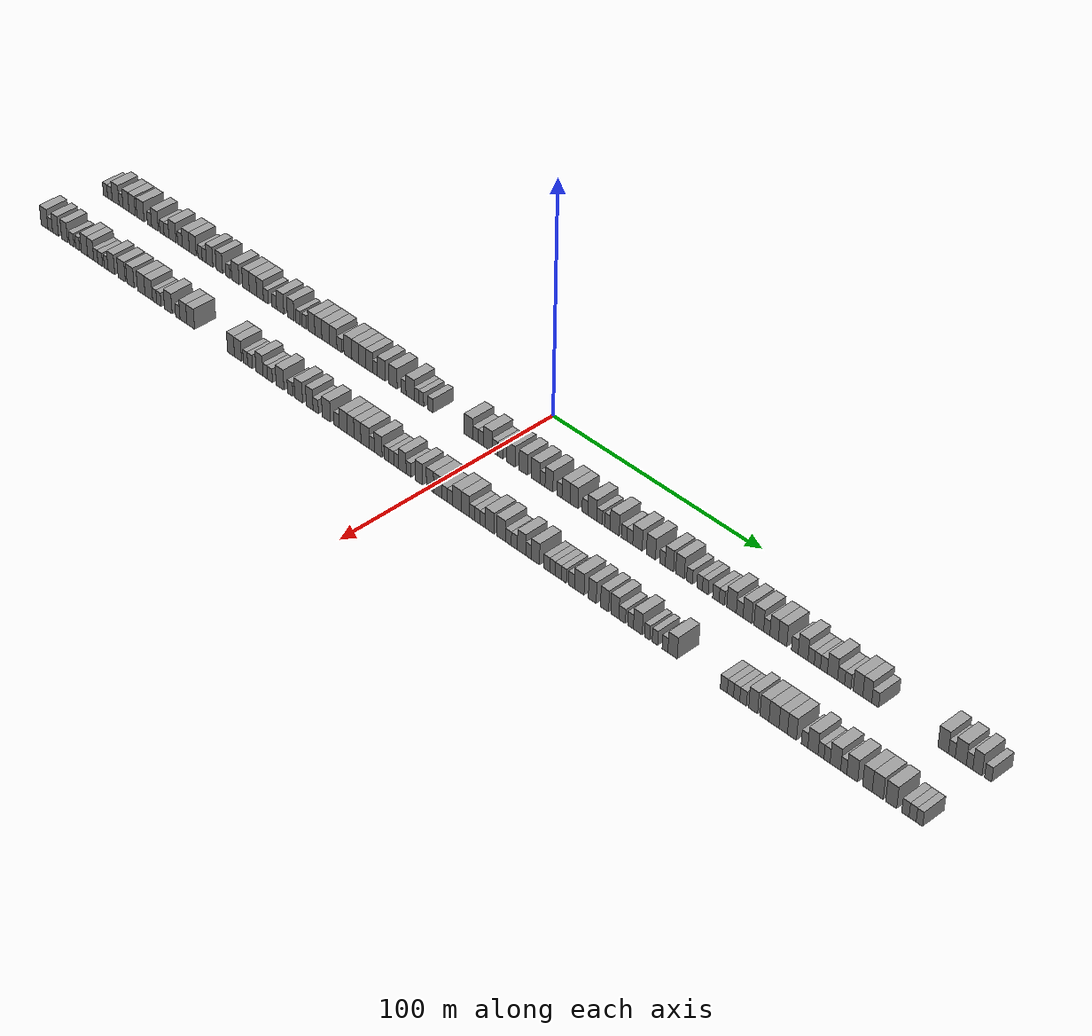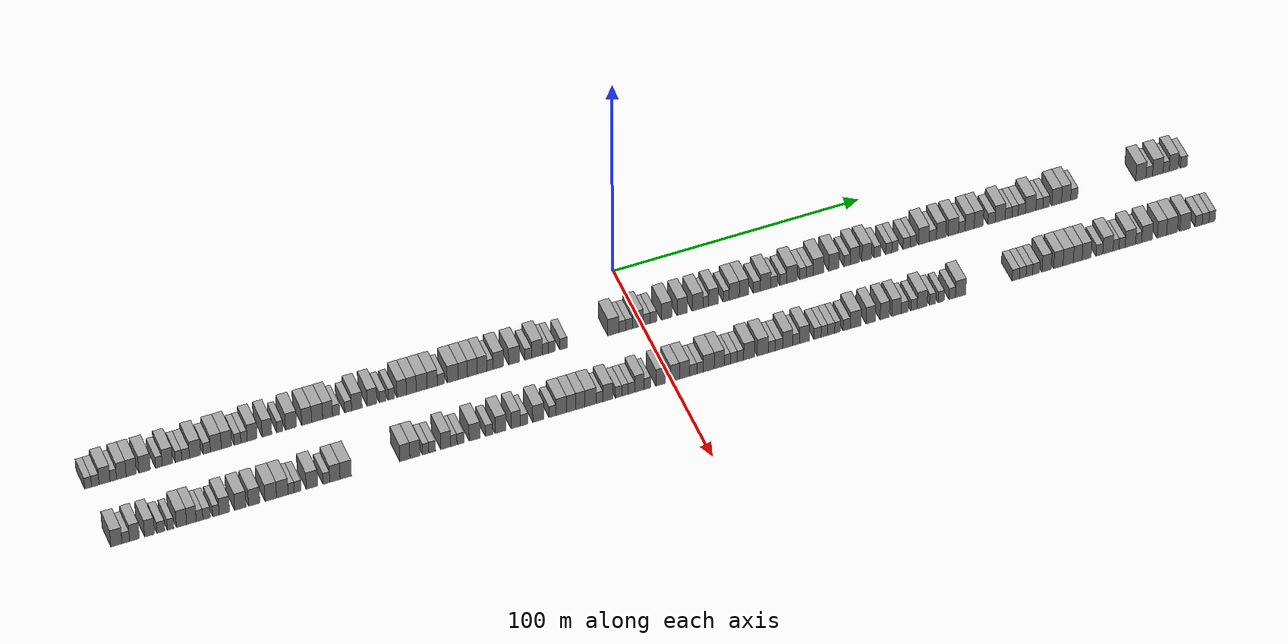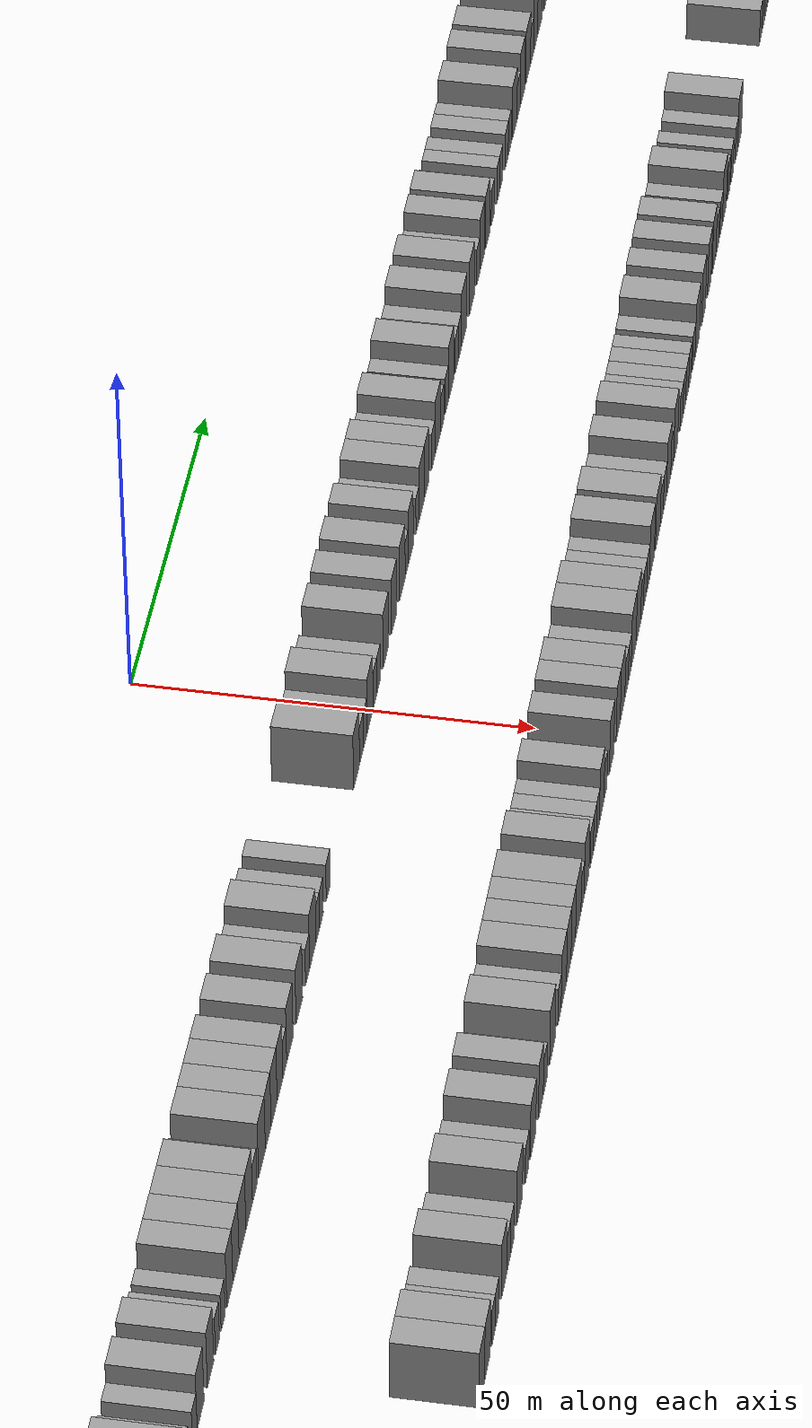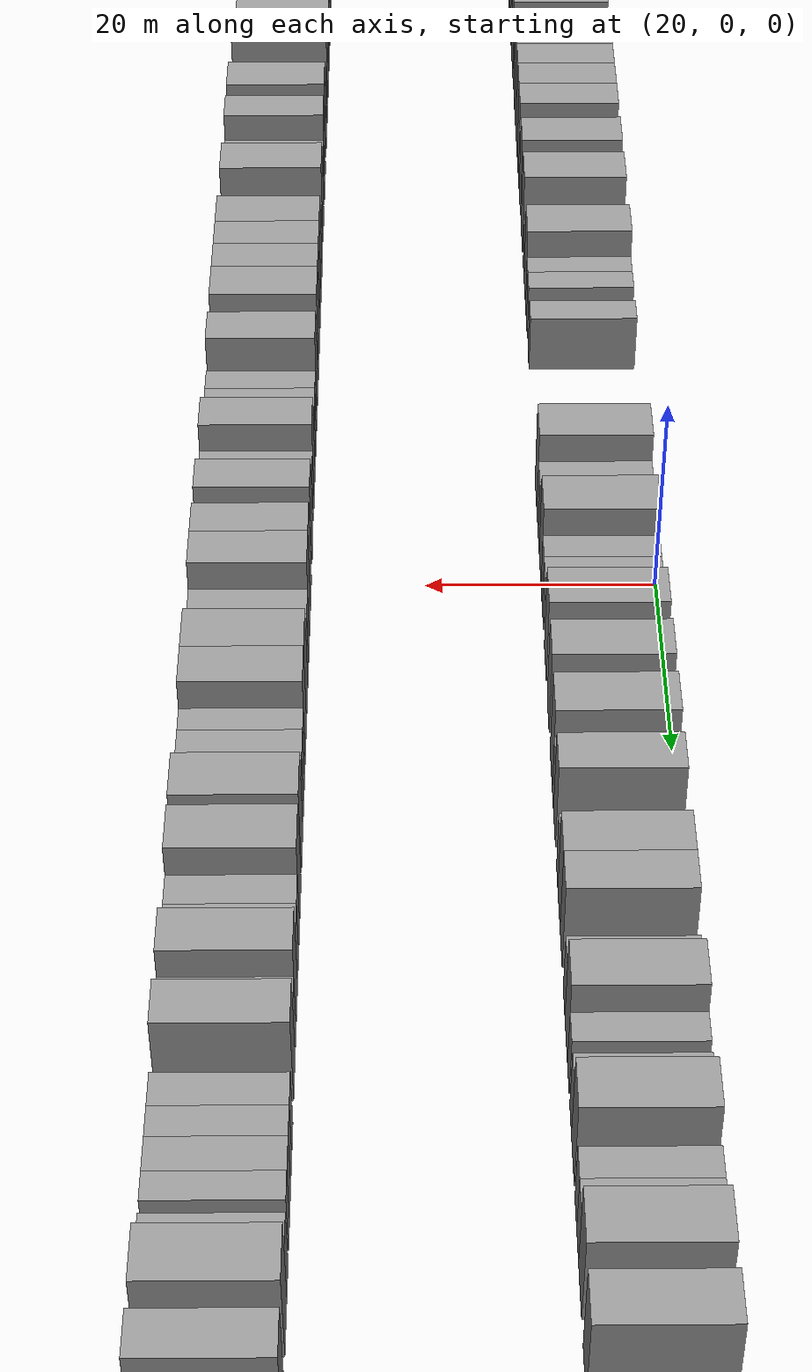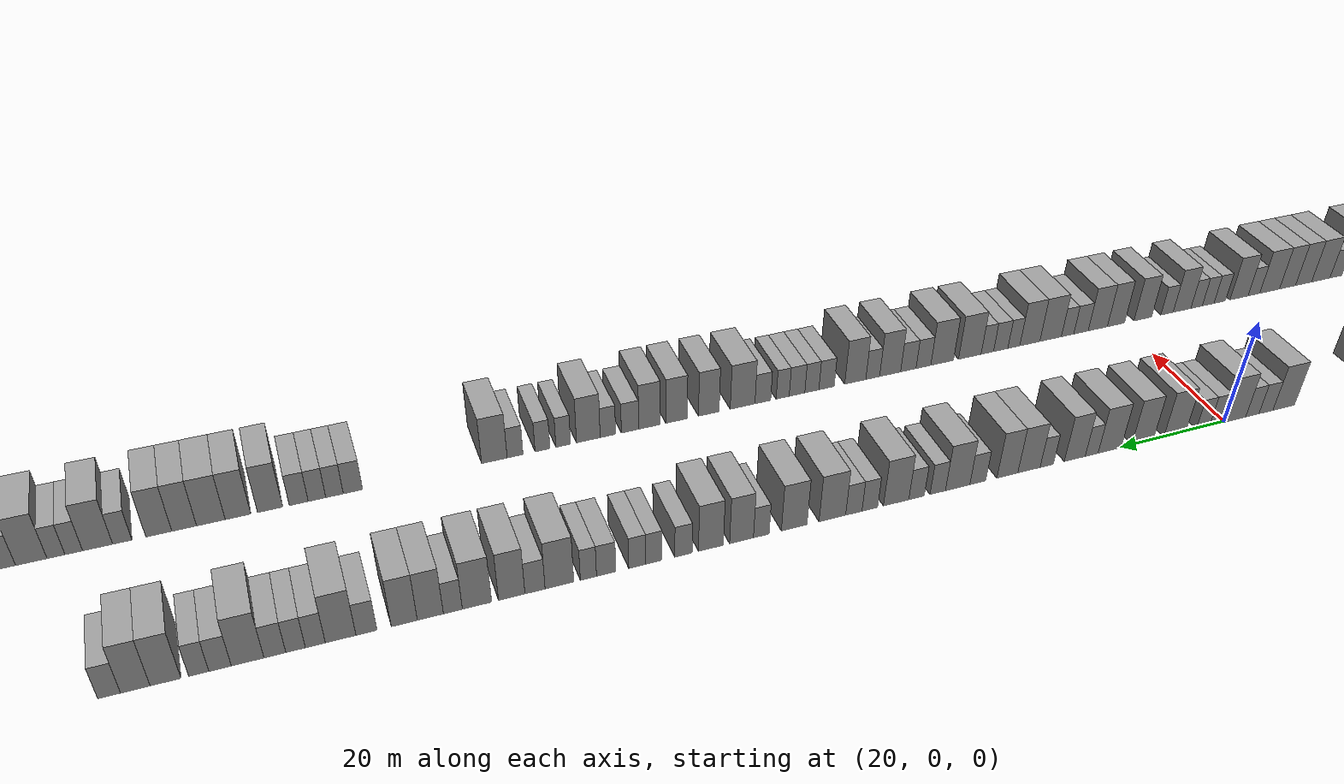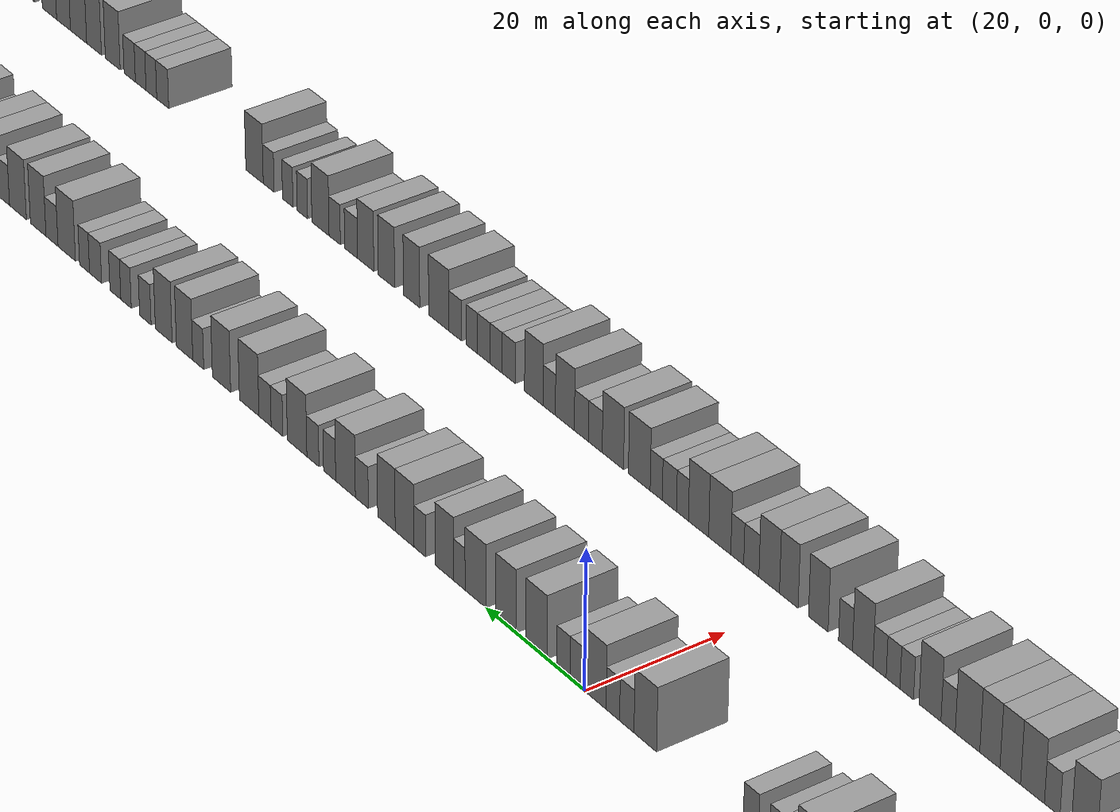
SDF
<sdf version="1.6">
 <world name="default">
  <scene>
   <sky><clouds><speed>12</speed></clouds></sky>
   <ambient>0.4 0.4 0.4 1</ambient>
   <background>0.7 0.7 0.7 1</background>
   <shadows>1</shadows>
  </scene>
  <gravity>0 0 -9.8066</gravity>
  <magnetic_field>6e-06 2.3e-05 -4.2e-05</magnetic_field>
  <physics default="0" name="default_physics" type="ode">
   <ode>
    <solver>
     <type>quick</type>
     <iters>10</iters>
     <sor>1.0</sor>
     <use_dynamic_moi_rescaling>0</use_dynamic_moi_rescaling>
    </solver>
    <constraints>
     <cfm>0</cfm>
     <erp>0.2</erp>
     <contact_max_correcting_vel>100</contact_max_correcting_vel>
     <contact_surface_layer>0.001</contact_surface_layer>
    </constraints>
   </ode>
   <max_step_size>0.004</max_step_size>
   <real_time_factor>1</real_time_factor>
   <real_time_update_rate>250</real_time_update_rate>
  </physics>
  <light name="sun" type="directional">
   <pose>0 0 10 0 0 0</pose>
   <diffuse>0.8 0.8 0.8 1</diffuse>
   <specular>0.2 0.2 0.2 1</specular>
   <attenuation>
    <range>1000</range>
    <constant>0.9</constant>
    <linear>0.01</linear>
    <quadratic>0.001</quadratic>
   </attenuation>
   <direction>-0.5 0.1 -0.9</direction>
  </light>
  <model name="building_1">
   <static>1</static>
   <pose>25.0000 -218.6765 0 0.000000 0.000000 0.000000</pose>
   <link name="link">
    <pose>0 0 3.00 0 0 0</pose>
    <collision name="collision"><geometry><box><size>10.0000 2.6469 6.0000</size></box></geometry></collision>
    <visual name="visual">
     <cast_shadows>0</cast_shadows>
     <geometry><box><size>10.0000 2.6469 6.0000</size></box></geometry>
     <material>
      <script>
       <uri>model://grey_wall/materials/scripts</uri>
       <uri>model://grey_wall/materials/textures</uri>
       <name>vrc/grey_wall</name>
      </script>
     </material>
    </visual>
   </link>
  </model>
  <model name="building_2">
   <static>1</static>
   <pose>25.0000 -215.8874 0 0.000000 0.000000 0.000000</pose>
   <link name="link">
    <pose>0 0 3.00 0 0 0</pose>
    <collision name="collision"><geometry><box><size>10.0000 2.9313 6.0000</size></box></geometry></collision>
    <visual name="visual">
     <cast_shadows>0</cast_shadows>
     <geometry><box><size>10.0000 2.9313 6.0000</size></box></geometry>
     <material>
      <script>
       <uri>model://grey_wall/materials/scripts</uri>
       <uri>model://grey_wall/materials/textures</uri>
       <name>vrc/grey_wall</name>
      </script>
     </material>
    </visual>
   </link>
  </model>
  <model name="building_3">
   <static>1</static>
   <pose>25.0000 -212.2901 0 0.000000 0.000000 0.000000</pose>
   <link name="link">
    <pose>0 0 4.50 0 0 0</pose>
    <collision name="collision"><geometry><box><size>10.0000 4.2634 9.0000</size></box></geometry></collision>
    <visual name="visual">
     <cast_shadows>0</cast_shadows>
     <geometry><box><size>10.0000 4.2634 9.0000</size></box></geometry>
     <material>
      <script>
       <uri>model://grey_wall/materials/scripts</uri>
       <uri>model://grey_wall/materials/textures</uri>
       <name>vrc/grey_wall</name>
      </script>
     </material>
    </visual>
   </link>
  </model>
  <model name="building_4">
   <static>1</static>
   <pose>25.0000 -208.8919 0 0.000000 0.000000 0.000000</pose>
   <link name="link">
    <pose>0 0 3.00 0 0 0</pose>
    <collision name="collision"><geometry><box><size>10.0000 2.5329 6.0000</size></box></geometry></collision>
    <visual name="visual">
     <cast_shadows>0</cast_shadows>
     <geometry><box><size>10.0000 2.5329 6.0000</size></box></geometry>
     <material>
      <script>
       <uri>model://grey_wall/materials/scripts</uri>
       <uri>model://grey_wall/materials/textures</uri>
       <name>vrc/grey_wall</name>
      </script>
     </material>
    </visual>
   </link>
  </model>
  <model name="building_5">
   <static>1</static>
   <pose>25.0000 -205.7682 0 0.000000 0.000000 0.000000</pose>
   <link name="link">
    <pose>0 0 4.50 0 0 0</pose>
    <collision name="collision"><geometry><box><size>10.0000 3.7144 9.0000</size></box></geometry></collision>
    <visual name="visual">
     <cast_shadows>0</cast_shadows>
     <geometry><box><size>10.0000 3.7144 9.0000</size></box></geometry>
     <material>
      <script>
       <uri>model://grey_wall/materials/scripts</uri>
       <uri>model://grey_wall/materials/textures</uri>
       <name>vrc/grey_wall</name>
      </script>
     </material>
    </visual>
   </link>
  </model>
  <model name="building_6">
   <static>1</static>
   <pose>25.0000 -201.9411 0 0.000000 0.000000 0.000000</pose>
   <link name="link">
    <pose>0 0 4.50 0 0 0</pose>
    <collision name="collision"><geometry><box><size>10.0000 3.9398 9.0000</size></box></geometry></collision>
    <visual name="visual">
     <cast_shadows>0</cast_shadows>
     <geometry><box><size>10.0000 3.9398 9.0000</size></box></geometry>
     <material>
      <script>
       <uri>model://grey_wall/materials/scripts</uri>
       <uri>model://grey_wall/materials/textures</uri>
       <name>vrc/grey_wall</name>
      </script>
     </material>
    </visual>
   </link>
  </model>
  <model name="building_7">
   <static>1</static>
   <pose>25.0000 -196.7519 0 0.000000 0.000000 0.000000</pose>
   <link name="link">
    <pose>0 0 4.50 0 0 0</pose>
    <collision name="collision"><geometry><box><size>10.0000 4.4386 9.0000</size></box></geometry></collision>
    <visual name="visual">
     <cast_shadows>0</cast_shadows>
     <geometry><box><size>10.0000 4.4386 9.0000</size></box></geometry>
     <material>
      <script>
       <uri>model://grey_wall/materials/scripts</uri>
       <uri>model://grey_wall/materials/textures</uri>
       <name>vrc/grey_wall</name>
      </script>
     </material>
    </visual>
   </link>
  </model>
  <model name="building_8">
   <static>1</static>
   <pose>25.0000 -191.2256 0 0.000000 0.000000 0.000000</pose>
   <link name="link">
    <pose>0 0 3.00 0 0 0</pose>
    <collision name="collision"><geometry><box><size>10.0000 2.6140 6.0000</size></box></geometry></collision>
    <visual name="visual">
     <cast_shadows>0</cast_shadows>
     <geometry><box><size>10.0000 2.6140 6.0000</size></box></geometry>
     <material>
      <script>
       <uri>model://grey_wall/materials/scripts</uri>
       <uri>model://grey_wall/materials/textures</uri>
       <name>vrc/grey_wall</name>
      </script>
     </material>
    </visual>
   </link>
  </model>
  <model name="building_9">
   <static>1</static>
   <pose>25.0000 -187.8880 0 0.000000 0.000000 0.000000</pose>
   <link name="link">
    <pose>0 0 4.50 0 0 0</pose>
    <collision name="collision"><geometry><box><size>10.0000 4.0611 9.0000</size></box></geometry></collision>
    <visual name="visual">
     <cast_shadows>0</cast_shadows>
     <geometry><box><size>10.0000 4.0611 9.0000</size></box></geometry>
     <material>
      <script>
       <uri>model://grey_wall/materials/scripts</uri>
       <uri>model://grey_wall/materials/textures</uri>
       <name>vrc/grey_wall</name>
      </script>
     </material>
    </visual>
   </link>
  </model>
  <model name="building_10">
   <static>1</static>
   <pose>25.0000 -183.5854 0 0.000000 0.000000 0.000000</pose>
   <link name="link">
    <pose>0 0 3.00 0 0 0</pose>
    <collision name="collision"><geometry><box><size>10.0000 2.5442 6.0000</size></box></geometry></collision>
    <visual name="visual">
     <cast_shadows>0</cast_shadows>
     <geometry><box><size>10.0000 2.5442 6.0000</size></box></geometry>
     <material>
      <script>
       <uri>model://grey_wall/materials/scripts</uri>
       <uri>model://grey_wall/materials/textures</uri>
       <name>vrc/grey_wall</name>
      </script>
     </material>
    </visual>
   </link>
  </model>
  <model name="building_11">
   <static>1</static>
   <pose>25.0000 -180.8187 0 0.000000 0.000000 0.000000</pose>
   <link name="link">
    <pose>0 0 3.00 0 0 0</pose>
    <collision name="collision"><geometry><box><size>10.0000 2.9892 6.0000</size></box></geometry></collision>
    <visual name="visual">
     <cast_shadows>0</cast_shadows>
     <geometry><box><size>10.0000 2.9892 6.0000</size></box></geometry>
     <material>
      <script>
       <uri>model://grey_wall/materials/scripts</uri>
       <uri>model://grey_wall/materials/textures</uri>
       <name>vrc/grey_wall</name>
      </script>
     </material>
    </visual>
   </link>
  </model>
  <model name="building_12">
   <static>1</static>
   <pose>25.0000 -177.1637 0 0.000000 0.000000 0.000000</pose>
   <link name="link">
    <pose>0 0 4.50 0 0 0</pose>
    <collision name="collision"><geometry><box><size>10.0000 4.3208 9.0000</size></box></geometry></collision>
    <visual name="visual">
     <cast_shadows>0</cast_shadows>
     <geometry><box><size>10.0000 4.3208 9.0000</size></box></geometry>
     <material>
      <script>
       <uri>model://grey_wall/materials/scripts</uri>
       <uri>model://grey_wall/materials/textures</uri>
       <name>vrc/grey_wall</name>
      </script>
     </material>
    </visual>
   </link>
  </model>
  <model name="building_13">
   <static>1</static>
   <pose>25.0000 -172.5812 0 0.000000 0.000000 0.000000</pose>
   <link name="link">
    <pose>0 0 3.00 0 0 0</pose>
    <collision name="collision"><geometry><box><size>10.0000 2.8442 6.0000</size></box></geometry></collision>
    <visual name="visual">
     <cast_shadows>0</cast_shadows>
     <geometry><box><size>10.0000 2.8442 6.0000</size></box></geometry>
     <material>
      <script>
       <uri>model://grey_wall/materials/scripts</uri>
       <uri>model://grey_wall/materials/textures</uri>
       <name>vrc/grey_wall</name>
      </script>
     </material>
    </visual>
   </link>
  </model>
  <model name="building_14">
   <static>1</static>
   <pose>25.0000 -169.0431 0 0.000000 0.000000 0.000000</pose>
   <link name="link">
    <pose>0 0 4.50 0 0 0</pose>
    <collision name="collision"><geometry><box><size>10.0000 4.2320 9.0000</size></box></geometry></collision>
    <visual name="visual">
     <cast_shadows>0</cast_shadows>
     <geometry><box><size>10.0000 4.2320 9.0000</size></box></geometry>
     <material>
      <script>
       <uri>model://grey_wall/materials/scripts</uri>
       <uri>model://grey_wall/materials/textures</uri>
       <name>vrc/grey_wall</name>
      </script>
     </material>
    </visual>
   </link>
  </model>
  <model name="building_15">
   <static>1</static>
   <pose>25.0000 -164.9125 0 0.000000 0.000000 0.000000</pose>
   <link name="link">
    <pose>0 0 4.50 0 0 0</pose>
    <collision name="collision"><geometry><box><size>10.0000 4.0294 9.0000</size></box></geometry></collision>
    <visual name="visual">
     <cast_shadows>0</cast_shadows>
     <geometry><box><size>10.0000 4.0294 9.0000</size></box></geometry>
     <material>
      <script>
       <uri>model://grey_wall/materials/scripts</uri>
       <uri>model://grey_wall/materials/textures</uri>
       <name>vrc/grey_wall</name>
      </script>
     </material>
    </visual>
   </link>
  </model>
  <model name="building_16">
   <static>1</static>
   <pose>25.0000 -160.6049 0 0.000000 0.000000 0.000000</pose>
   <link name="link">
    <pose>0 0 3.00 0 0 0</pose>
    <collision name="collision"><geometry><box><size>10.0000 2.5857 6.0000</size></box></geometry></collision>
    <visual name="visual">
     <cast_shadows>0</cast_shadows>
     <geometry><box><size>10.0000 2.5857 6.0000</size></box></geometry>
     <material>
      <script>
       <uri>model://grey_wall/materials/scripts</uri>
       <uri>model://grey_wall/materials/textures</uri>
       <name>vrc/grey_wall</name>
      </script>
     </material>
    </visual>
   </link>
  </model>
  <model name="building_17">
   <static>1</static>
   <pose>25.0000 -158.0587 0 0.000000 0.000000 0.000000</pose>
   <link name="link">
    <pose>0 0 3.00 0 0 0</pose>
    <collision name="collision"><geometry><box><size>10.0000 2.5066 6.0000</size></box></geometry></collision>
    <visual name="visual">
     <cast_shadows>0</cast_shadows>
     <geometry><box><size>10.0000 2.5066 6.0000</size></box></geometry>
     <material>
      <script>
       <uri>model://grey_wall/materials/scripts</uri>
       <uri>model://grey_wall/materials/textures</uri>
       <name>vrc/grey_wall</name>
      </script>
     </material>
    </visual>
   </link>
  </model>
  <model name="building_18">
   <static>1</static>
   <pose>25.0000 -154.8702 0 0.000000 0.000000 0.000000</pose>
   <link name="link">
    <pose>0 0 4.50 0 0 0</pose>
    <collision name="collision"><geometry><box><size>10.0000 3.8704 9.0000</size></box></geometry></collision>
    <visual name="visual">
     <cast_shadows>0</cast_shadows>
     <geometry><box><size>10.0000 3.8704 9.0000</size></box></geometry>
     <material>
      <script>
       <uri>model://grey_wall/materials/scripts</uri>
       <uri>model://grey_wall/materials/textures</uri>
       <name>vrc/grey_wall</name>
      </script>
     </material>
    </visual>
   </link>
  </model>
  <model name="building_19">
   <static>1</static>
   <pose>25.0000 -149.0745 0 0.000000 0.000000 0.000000</pose>
   <link name="link">
    <pose>0 0 4.50 0 0 0</pose>
    <collision name="collision"><geometry><box><size>10.0000 3.7209 9.0000</size></box></geometry></collision>
    <visual name="visual">
     <cast_shadows>0</cast_shadows>
     <geometry><box><size>10.0000 3.7209 9.0000</size></box></geometry>
     <material>
      <script>
       <uri>model://grey_wall/materials/scripts</uri>
       <uri>model://grey_wall/materials/textures</uri>
       <name>vrc/grey_wall</name>
      </script>
     </material>
    </visual>
   </link>
  </model>
  <model name="building_20">
   <static>1</static>
   <pose>25.0000 -144.0134 0 0.000000 0.000000 0.000000</pose>
   <link name="link">
    <pose>0 0 3.00 0 0 0</pose>
    <collision name="collision"><geometry><box><size>10.0000 2.4014 6.0000</size></box></geometry></collision>
    <visual name="visual">
     <cast_shadows>0</cast_shadows>
     <geometry><box><size>10.0000 2.4014 6.0000</size></box></geometry>
     <material>
      <script>
       <uri>model://grey_wall/materials/scripts</uri>
       <uri>model://grey_wall/materials/textures</uri>
       <name>vrc/grey_wall</name>
      </script>
     </material>
    </visual>
   </link>
  </model>
  <model name="building_21">
   <static>1</static>
   <pose>25.0000 -139.6364 0 0.000000 0.000000 0.000000</pose>
   <link name="link">
    <pose>0 0 4.50 0 0 0</pose>
    <collision name="collision"><geometry><box><size>10.0000 4.3525 9.0000</size></box></geometry></collision>
    <visual name="visual">
     <cast_shadows>0</cast_shadows>
     <geometry><box><size>10.0000 4.3525 9.0000</size></box></geometry>
     <material>
      <script>
       <uri>model://grey_wall/materials/scripts</uri>
       <uri>model://grey_wall/materials/textures</uri>
       <name>vrc/grey_wall</name>
      </script>
     </material>
    </visual>
   </link>
  </model>
  <model name="building_22">
   <static>1</static>
   <pose>25.0000 -133.5092 0 0.000000 0.000000 0.000000</pose>
   <link name="link">
    <pose>0 0 4.50 0 0 0</pose>
    <collision name="collision"><geometry><box><size>10.0000 3.9018 9.0000</size></box></geometry></collision>
    <visual name="visual">
     <cast_shadows>0</cast_shadows>
     <geometry><box><size>10.0000 3.9018 9.0000</size></box></geometry>
     <material>
      <script>
       <uri>model://grey_wall/materials/scripts</uri>
       <uri>model://grey_wall/materials/textures</uri>
       <name>vrc/grey_wall</name>
      </script>
     </material>
    </visual>
   </link>
  </model>
  <model name="building_23">
   <static>1</static>
   <pose>25.0000 -129.3947 0 0.000000 0.000000 0.000000</pose>
   <link name="link">
    <pose>0 0 4.50 0 0 0</pose>
    <collision name="collision"><geometry><box><size>10.0000 4.3272 9.0000</size></box></geometry></collision>
    <visual name="visual">
     <cast_shadows>0</cast_shadows>
     <geometry><box><size>10.0000 4.3272 9.0000</size></box></geometry>
     <material>
      <script>
       <uri>model://grey_wall/materials/scripts</uri>
       <uri>model://grey_wall/materials/textures</uri>
       <name>vrc/grey_wall</name>
      </script>
     </material>
    </visual>
   </link>
  </model>
  <model name="building_24">
   <static>1</static>
   <pose>25.0000 -125.3055 0 0.000000 0.000000 0.000000</pose>
   <link name="link">
    <pose>0 0 4.50 0 0 0</pose>
    <collision name="collision"><geometry><box><size>10.0000 3.8513 9.0000</size></box></geometry></collision>
    <visual name="visual">
     <cast_shadows>0</cast_shadows>
     <geometry><box><size>10.0000 3.8513 9.0000</size></box></geometry>
     <material>
      <script>
       <uri>model://grey_wall/materials/scripts</uri>
       <uri>model://grey_wall/materials/textures</uri>
       <name>vrc/grey_wall</name>
      </script>
     </material>
    </visual>
   </link>
  </model>
  <model name="building_25">
   <static>1</static>
   <pose>25.0000 -121.9807 0 0.000000 0.000000 0.000000</pose>
   <link name="link">
    <pose>0 0 3.00 0 0 0</pose>
    <collision name="collision"><geometry><box><size>10.0000 2.7983 6.0000</size></box></geometry></collision>
    <visual name="visual">
     <cast_shadows>0</cast_shadows>
     <geometry><box><size>10.0000 2.7983 6.0000</size></box></geometry>
     <material>
      <script>
       <uri>model://grey_wall/materials/scripts</uri>
       <uri>model://grey_wall/materials/textures</uri>
       <name>vrc/grey_wall</name>
      </script>
     </material>
    </visual>
   </link>
  </model>
  <model name="building_26">
   <static>1</static>
   <pose>25.0000 -117.2089 0 0.000000 0.000000 0.000000</pose>
   <link name="link">
    <pose>0 0 3.00 0 0 0</pose>
    <collision name="collision"><geometry><box><size>10.0000 2.7454 6.0000</size></box></geometry></collision>
    <visual name="visual">
     <cast_shadows>0</cast_shadows>
     <geometry><box><size>10.0000 2.7454 6.0000</size></box></geometry>
     <material>
      <script>
       <uri>model://grey_wall/materials/scripts</uri>
       <uri>model://grey_wall/materials/textures</uri>
       <name>vrc/grey_wall</name>
      </script>
     </material>
    </visual>
   </link>
  </model>
  <model name="building_27">
   <static>1</static>
   <pose>25.0000 -113.7824 0 0.000000 0.000000 0.000000</pose>
   <link name="link">
    <pose>0 0 4.50 0 0 0</pose>
    <collision name="collision"><geometry><box><size>10.0000 4.1076 9.0000</size></box></geometry></collision>
    <visual name="visual">
     <cast_shadows>0</cast_shadows>
     <geometry><box><size>10.0000 4.1076 9.0000</size></box></geometry>
     <material>
      <script>
       <uri>model://grey_wall/materials/scripts</uri>
       <uri>model://grey_wall/materials/textures</uri>
       <name>vrc/grey_wall</name>
      </script>
     </material>
    </visual>
   </link>
  </model>
  <model name="building_28">
   <static>1</static>
   <pose>25.0000 -107.8168 0 0.000000 0.000000 0.000000</pose>
   <link name="link">
    <pose>0 0 4.50 0 0 0</pose>
    <collision name="collision"><geometry><box><size>10.0000 3.8236 9.0000</size></box></geometry></collision>
    <visual name="visual">
     <cast_shadows>0</cast_shadows>
     <geometry><box><size>10.0000 3.8236 9.0000</size></box></geometry>
     <material>
      <script>
       <uri>model://grey_wall/materials/scripts</uri>
       <uri>model://grey_wall/materials/textures</uri>
       <name>vrc/grey_wall</name>
      </script>
     </material>
    </visual>
   </link>
  </model>
  <model name="building_29">
   <static>1</static>
   <pose>25.0000 -103.6696 0 0.000000 0.000000 0.000000</pose>
   <link name="link">
    <pose>0 0 3.00 0 0 0</pose>
    <collision name="collision"><geometry><box><size>10.0000 2.4709 6.0000</size></box></geometry></collision>
    <visual name="visual">
     <cast_shadows>0</cast_shadows>
     <geometry><box><size>10.0000 2.4709 6.0000</size></box></geometry>
     <material>
      <script>
       <uri>model://grey_wall/materials/scripts</uri>
       <uri>model://grey_wall/materials/textures</uri>
       <name>vrc/grey_wall</name>
      </script>
     </material>
    </visual>
   </link>
  </model>
  <model name="building_30">
   <static>1</static>
   <pose>25.0000 -100.1896 0 0.000000 0.000000 0.000000</pose>
   <link name="link">
    <pose>0 0 3.00 0 0 0</pose>
    <collision name="collision"><geometry><box><size>10.0000 2.4890 6.0000</size></box></geometry></collision>
    <visual name="visual">
     <cast_shadows>0</cast_shadows>
     <geometry><box><size>10.0000 2.4890 6.0000</size></box></geometry>
     <material>
      <script>
       <uri>model://grey_wall/materials/scripts</uri>
       <uri>model://grey_wall/materials/textures</uri>
       <name>vrc/grey_wall</name>
      </script>
     </material>
    </visual>
   </link>
  </model>
  <model name="building_31">
   <static>1</static>
   <pose>25.0000 -96.0738 0 0.000000 0.000000 0.000000</pose>
   <link name="link">
    <pose>0 0 4.50 0 0 0</pose>
    <collision name="collision"><geometry><box><size>10.0000 3.7427 9.0000</size></box></geometry></collision>
    <visual name="visual">
     <cast_shadows>0</cast_shadows>
     <geometry><box><size>10.0000 3.7427 9.0000</size></box></geometry>
     <material>
      <script>
       <uri>model://grey_wall/materials/scripts</uri>
       <uri>model://grey_wall/materials/textures</uri>
       <name>vrc/grey_wall</name>
      </script>
     </material>
    </visual>
   </link>
  </model>
  <model name="building_32">
   <static>1</static>
   <pose>25.0000 -92.2656 0 0.000000 0.000000 0.000000</pose>
   <link name="link">
    <pose>0 0 4.50 0 0 0</pose>
    <collision name="collision"><geometry><box><size>10.0000 3.8736 9.0000</size></box></geometry></collision>
    <visual name="visual">
     <cast_shadows>0</cast_shadows>
     <geometry><box><size>10.0000 3.8736 9.0000</size></box></geometry>
     <material>
      <script>
       <uri>model://grey_wall/materials/scripts</uri>
       <uri>model://grey_wall/materials/textures</uri>
       <name>vrc/grey_wall</name>
      </script>
     </material>
    </visual>
   </link>
  </model>
  <model name="building_33">
   <static>1</static>
   <pose>25.0000 -88.1891 0 0.000000 0.000000 0.000000</pose>
   <link name="link">
    <pose>0 0 4.50 0 0 0</pose>
    <collision name="collision"><geometry><box><size>10.0000 4.2794 9.0000</size></box></geometry></collision>
    <visual name="visual">
     <cast_shadows>0</cast_shadows>
     <geometry><box><size>10.0000 4.2794 9.0000</size></box></geometry>
     <material>
      <script>
       <uri>model://grey_wall/materials/scripts</uri>
       <uri>model://grey_wall/materials/textures</uri>
       <name>vrc/grey_wall</name>
      </script>
     </material>
    </visual>
   </link>
  </model>
  <model name="building_34">
   <static>1</static>
   <pose>25.0000 -84.0061 0 0.000000 0.000000 0.000000</pose>
   <link name="link">
    <pose>0 0 4.50 0 0 0</pose>
    <collision name="collision"><geometry><box><size>10.0000 4.0865 9.0000</size></box></geometry></collision>
    <visual name="visual">
     <cast_shadows>0</cast_shadows>
     <geometry><box><size>10.0000 4.0865 9.0000</size></box></geometry>
     <material>
      <script>
       <uri>model://grey_wall/materials/scripts</uri>
       <uri>model://grey_wall/materials/textures</uri>
       <name>vrc/grey_wall</name>
      </script>
     </material>
    </visual>
   </link>
  </model>
  <model name="building_35">
   <static>1</static>
   <pose>25.0000 -80.5269 0 0.000000 0.000000 0.000000</pose>
   <link name="link">
    <pose>0 0 3.00 0 0 0</pose>
    <collision name="collision"><geometry><box><size>10.0000 2.8718 6.0000</size></box></geometry></collision>
    <visual name="visual">
     <cast_shadows>0</cast_shadows>
     <geometry><box><size>10.0000 2.8718 6.0000</size></box></geometry>
     <material>
      <script>
       <uri>model://grey_wall/materials/scripts</uri>
       <uri>model://grey_wall/materials/textures</uri>
       <name>vrc/grey_wall</name>
      </script>
     </material>
    </visual>
   </link>
  </model>
  <model name="building_36">
   <static>1</static>
   <pose>25.0000 -75.9155 0 0.000000 0.000000 0.000000</pose>
   <link name="link">
    <pose>0 0 4.50 0 0 0</pose>
    <collision name="collision"><geometry><box><size>10.0000 4.3510 9.0000</size></box></geometry></collision>
    <visual name="visual">
     <cast_shadows>0</cast_shadows>
     <geometry><box><size>10.0000 4.3510 9.0000</size></box></geometry>
     <material>
      <script>
       <uri>model://grey_wall/materials/scripts</uri>
       <uri>model://grey_wall/materials/textures</uri>
       <name>vrc/grey_wall</name>
      </script>
     </material>
    </visual>
   </link>
  </model>
  <model name="building_37">
   <static>1</static>
   <pose>25.0000 -71.8836 0 0.000000 0.000000 0.000000</pose>
   <link name="link">
    <pose>0 0 4.50 0 0 0</pose>
    <collision name="collision"><geometry><box><size>10.0000 3.7129 9.0000</size></box></geometry></collision>
    <visual name="visual">
     <cast_shadows>0</cast_shadows>
     <geometry><box><size>10.0000 3.7129 9.0000</size></box></geometry>
     <material>
      <script>
       <uri>model://grey_wall/materials/scripts</uri>
       <uri>model://grey_wall/materials/textures</uri>
       <name>vrc/grey_wall</name>
      </script>
     </material>
    </visual>
   </link>
  </model>
  <model name="building_38">
   <static>1</static>
   <pose>25.0000 -68.0670 0 0.000000 0.000000 0.000000</pose>
   <link name="link">
    <pose>0 0 4.50 0 0 0</pose>
    <collision name="collision"><geometry><box><size>10.0000 3.9202 9.0000</size></box></geometry></collision>
    <visual name="visual">
     <cast_shadows>0</cast_shadows>
     <geometry><box><size>10.0000 3.9202 9.0000</size></box></geometry>
     <material>
      <script>
       <uri>model://grey_wall/materials/scripts</uri>
       <uri>model://grey_wall/materials/textures</uri>
       <name>vrc/grey_wall</name>
      </script>
     </material>
    </visual>
   </link>
  </model>
  <model name="building_39">
   <static>1</static>
   <pose>25.0000 -64.2276 0 0.000000 0.000000 0.000000</pose>
   <link name="link">
    <pose>0 0 4.50 0 0 0</pose>
    <collision name="collision"><geometry><box><size>10.0000 3.7588 9.0000</size></box></geometry></collision>
    <visual name="visual">
     <cast_shadows>0</cast_shadows>
     <geometry><box><size>10.0000 3.7588 9.0000</size></box></geometry>
     <material>
      <script>
       <uri>model://grey_wall/materials/scripts</uri>
       <uri>model://grey_wall/materials/textures</uri>
       <name>vrc/grey_wall</name>
      </script>
     </material>
    </visual>
   </link>
  </model>
  <model name="building_40">
   <static>1</static>
   <pose>25.0000 -61.0948 0 0.000000 0.000000 0.000000</pose>
   <link name="link">
    <pose>0 0 3.00 0 0 0</pose>
    <collision name="collision"><geometry><box><size>10.0000 2.5068 6.0000</size></box></geometry></collision>
    <visual name="visual">
     <cast_shadows>0</cast_shadows>
     <geometry><box><size>10.0000 2.5068 6.0000</size></box></geometry>
     <material>
      <script>
       <uri>model://grey_wall/materials/scripts</uri>
       <uri>model://grey_wall/materials/textures</uri>
       <name>vrc/grey_wall</name>
      </script>
     </material>
    </visual>
   </link>
  </model>
  <model name="building_41">
   <static>1</static>
   <pose>25.0000 -57.7386 0 0.000000 0.000000 0.000000</pose>
   <link name="link">
    <pose>0 0 4.50 0 0 0</pose>
    <collision name="collision"><geometry><box><size>10.0000 4.2054 9.0000</size></box></geometry></collision>
    <visual name="visual">
     <cast_shadows>0</cast_shadows>
     <geometry><box><size>10.0000 4.2054 9.0000</size></box></geometry>
     <material>
      <script>
       <uri>model://grey_wall/materials/scripts</uri>
       <uri>model://grey_wall/materials/textures</uri>
       <name>vrc/grey_wall</name>
      </script>
     </material>
    </visual>
   </link>
  </model>
  <model name="building_42">
   <static>1</static>
   <pose>25.0000 -51.4354 0 0.000000 0.000000 0.000000</pose>
   <link name="link">
    <pose>0 0 4.50 0 0 0</pose>
    <collision name="collision"><geometry><box><size>10.0000 4.4011 9.0000</size></box></geometry></collision>
    <visual name="visual">
     <cast_shadows>0</cast_shadows>
     <geometry><box><size>10.0000 4.4011 9.0000</size></box></geometry>
     <material>
      <script>
       <uri>model://grey_wall/materials/scripts</uri>
       <uri>model://grey_wall/materials/textures</uri>
       <name>vrc/grey_wall</name>
      </script>
     </material>
    </visual>
   </link>
  </model>
  <model name="building_43">
   <static>1</static>
   <pose>25.0000 -45.8869 0 0.000000 0.000000 0.000000</pose>
   <link name="link">
    <pose>0 0 3.00 0 0 0</pose>
    <collision name="collision"><geometry><box><size>10.0000 2.6959 6.0000</size></box></geometry></collision>
    <visual name="visual">
     <cast_shadows>0</cast_shadows>
     <geometry><box><size>10.0000 2.6959 6.0000</size></box></geometry>
     <material>
      <script>
       <uri>model://grey_wall/materials/scripts</uri>
       <uri>model://grey_wall/materials/textures</uri>
       <name>vrc/grey_wall</name>
      </script>
     </material>
    </visual>
   </link>
  </model>
  <model name="building_44">
   <static>1</static>
   <pose>25.0000 -42.3355 0 0.000000 0.000000 0.000000</pose>
   <link name="link">
    <pose>0 0 4.50 0 0 0</pose>
    <collision name="collision"><geometry><box><size>10.0000 4.4068 9.0000</size></box></geometry></collision>
    <visual name="visual">
     <cast_shadows>0</cast_shadows>
     <geometry><box><size>10.0000 4.4068 9.0000</size></box></geometry>
     <material>
      <script>
       <uri>model://grey_wall/materials/scripts</uri>
       <uri>model://grey_wall/materials/textures</uri>
       <name>vrc/grey_wall</name>
      </script>
     </material>
    </visual>
   </link>
  </model>
  <model name="building_45">
   <static>1</static>
   <pose>25.0000 -38.9299 0 0.000000 0.000000 0.000000</pose>
   <link name="link">
    <pose>0 0 3.00 0 0 0</pose>
    <collision name="collision"><geometry><box><size>10.0000 2.4043 6.0000</size></box></geometry></collision>
    <visual name="visual">
     <cast_shadows>0</cast_shadows>
     <geometry><box><size>10.0000 2.4043 6.0000</size></box></geometry>
     <material>
      <script>
       <uri>model://grey_wall/materials/scripts</uri>
       <uri>model://grey_wall/materials/textures</uri>
       <name>vrc/grey_wall</name>
      </script>
     </material>
    </visual>
   </link>
  </model>
  <model name="building_46">
   <static>1</static>
   <pose>25.0000 -36.4468 0 0.000000 0.000000 0.000000</pose>
   <link name="link">
    <pose>0 0 3.00 0 0 0</pose>
    <collision name="collision"><geometry><box><size>10.0000 2.5620 6.0000</size></box></geometry></collision>
    <visual name="visual">
     <cast_shadows>0</cast_shadows>
     <geometry><box><size>10.0000 2.5620 6.0000</size></box></geometry>
     <material>
      <script>
       <uri>model://grey_wall/materials/scripts</uri>
       <uri>model://grey_wall/materials/textures</uri>
       <name>vrc/grey_wall</name>
      </script>
     </material>
    </visual>
   </link>
  </model>
  <model name="building_47">
   <static>1</static>
   <pose>25.0000 -31.7470 0 0.000000 0.000000 0.000000</pose>
   <link name="link">
    <pose>0 0 3.00 0 0 0</pose>
    <collision name="collision"><geometry><box><size>10.0000 2.8375 6.0000</size></box></geometry></collision>
    <visual name="visual">
     <cast_shadows>0</cast_shadows>
     <geometry><box><size>10.0000 2.8375 6.0000</size></box></geometry>
     <material>
      <script>
       <uri>model://grey_wall/materials/scripts</uri>
       <uri>model://grey_wall/materials/textures</uri>
       <name>vrc/grey_wall</name>
      </script>
     </material>
    </visual>
   </link>
  </model>
  <model name="building_48">
   <static>1</static>
   <pose>25.0000 -11.7976 0 0.000000 0.000000 0.000000</pose>
   <link name="link">
    <pose>0 0 4.50 0 0 0</pose>
    <collision name="collision"><geometry><box><size>10.0000 4.3538 9.0000</size></box></geometry></collision>
    <visual name="visual">
     <cast_shadows>0</cast_shadows>
     <geometry><box><size>10.0000 4.3538 9.0000</size></box></geometry>
     <material>
      <script>
       <uri>model://grey_wall/materials/scripts</uri>
       <uri>model://grey_wall/materials/textures</uri>
       <name>vrc/grey_wall</name>
      </script>
     </material>
    </visual>
   </link>
  </model>
  <model name="building_49">
   <static>1</static>
   <pose>25.0000 -8.2240 0 0.000000 0.000000 0.000000</pose>
   <link name="link">
    <pose>0 0 3.00 0 0 0</pose>
    <collision name="collision"><geometry><box><size>10.0000 2.7933 6.0000</size></box></geometry></collision>
    <visual name="visual">
     <cast_shadows>0</cast_shadows>
     <geometry><box><size>10.0000 2.7933 6.0000</size></box></geometry>
     <material>
      <script>
       <uri>model://grey_wall/materials/scripts</uri>
       <uri>model://grey_wall/materials/textures</uri>
       <name>vrc/grey_wall</name>
      </script>
     </material>
    </visual>
   </link>
  </model>
  <model name="building_50">
   <static>1</static>
   <pose>25.0000 -5.5053 0 0.000000 0.000000 0.000000</pose>
   <link name="link">
    <pose>0 0 3.00 0 0 0</pose>
    <collision name="collision"><geometry><box><size>10.0000 2.6441 6.0000</size></box></geometry></collision>
    <visual name="visual">
     <cast_shadows>0</cast_shadows>
     <geometry><box><size>10.0000 2.6441 6.0000</size></box></geometry>
     <material>
      <script>
       <uri>model://grey_wall/materials/scripts</uri>
       <uri>model://grey_wall/materials/textures</uri>
       <name>vrc/grey_wall</name>
      </script>
     </material>
    </visual>
   </link>
  </model>
  <model name="building_51">
   <static>1</static>
   <pose>25.0000 -1.9805 0 0.000000 0.000000 0.000000</pose>
   <link name="link">
    <pose>0 0 4.50 0 0 0</pose>
    <collision name="collision"><geometry><box><size>10.0000 4.4055 9.0000</size></box></geometry></collision>
    <visual name="visual">
     <cast_shadows>0</cast_shadows>
     <geometry><box><size>10.0000 4.4055 9.0000</size></box></geometry>
     <material>
      <script>
       <uri>model://grey_wall/materials/scripts</uri>
       <uri>model://grey_wall/materials/textures</uri>
       <name>vrc/grey_wall</name>
      </script>
     </material>
    </visual>
   </link>
  </model>
  <model name="building_52">
   <static>1</static>
   <pose>25.0000 1.5876 0 0.000000 0.000000 0.000000</pose>
   <link name="link">
    <pose>0 0 3.00 0 0 0</pose>
    <collision name="collision"><geometry><box><size>10.0000 2.7308 6.0000</size></box></geometry></collision>
    <visual name="visual">
     <cast_shadows>0</cast_shadows>
     <geometry><box><size>10.0000 2.7308 6.0000</size></box></geometry>
     <material>
      <script>
       <uri>model://grey_wall/materials/scripts</uri>
       <uri>model://grey_wall/materials/textures</uri>
       <name>vrc/grey_wall</name>
      </script>
     </material>
    </visual>
   </link>
  </model>
  <model name="building_53">
   <static>1</static>
   <pose>25.0000 4.2587 0 0.000000 0.000000 0.000000</pose>
   <link name="link">
    <pose>0 0 3.00 0 0 0</pose>
    <collision name="collision"><geometry><box><size>10.0000 2.6114 6.0000</size></box></geometry></collision>
    <visual name="visual">
     <cast_shadows>0</cast_shadows>
     <geometry><box><size>10.0000 2.6114 6.0000</size></box></geometry>
     <material>
      <script>
       <uri>model://grey_wall/materials/scripts</uri>
       <uri>model://grey_wall/materials/textures</uri>
       <name>vrc/grey_wall</name>
      </script>
     </material>
    </visual>
   </link>
  </model>
  <model name="building_54">
   <static>1</static>
   <pose>25.0000 9.6952 0 0.000000 0.000000 0.000000</pose>
   <link name="link">
    <pose>0 0 4.50 0 0 0</pose>
    <collision name="collision"><geometry><box><size>10.0000 4.2614 9.0000</size></box></geometry></collision>
    <visual name="visual">
     <cast_shadows>0</cast_shadows>
     <geometry><box><size>10.0000 4.2614 9.0000</size></box></geometry>
     <material>
      <script>
       <uri>model://grey_wall/materials/scripts</uri>
       <uri>model://grey_wall/materials/textures</uri>
       <name>vrc/grey_wall</name>
      </script>
     </material>
    </visual>
   </link>
  </model>
  <model name="building_55">
   <static>1</static>
   <pose>25.0000 15.8820 0 0.000000 0.000000 0.000000</pose>
   <link name="link">
    <pose>0 0 4.50 0 0 0</pose>
    <collision name="collision"><geometry><box><size>10.0000 4.1123 9.0000</size></box></geometry></collision>
    <visual name="visual">
     <cast_shadows>0</cast_shadows>
     <geometry><box><size>10.0000 4.1123 9.0000</size></box></geometry>
     <material>
      <script>
       <uri>model://grey_wall/materials/scripts</uri>
       <uri>model://grey_wall/materials/textures</uri>
       <name>vrc/grey_wall</name>
      </script>
     </material>
    </visual>
   </link>
  </model>
  <model name="building_56">
   <static>1</static>
   <pose>25.0000 22.0981 0 0.000000 0.000000 0.000000</pose>
   <link name="link">
    <pose>0 0 4.50 0 0 0</pose>
    <collision name="collision"><geometry><box><size>10.0000 4.3200 9.0000</size></box></geometry></collision>
    <visual name="visual">
     <cast_shadows>0</cast_shadows>
     <geometry><box><size>10.0000 4.3200 9.0000</size></box></geometry>
     <material>
      <script>
       <uri>model://grey_wall/materials/scripts</uri>
       <uri>model://grey_wall/materials/textures</uri>
       <name>vrc/grey_wall</name>
      </script>
     </material>
    </visual>
   </link>
  </model>
  <model name="building_57">
   <static>1</static>
   <pose>25.0000 25.4581 0 0.000000 0.000000 0.000000</pose>
   <link name="link">
    <pose>0 0 3.00 0 0 0</pose>
    <collision name="collision"><geometry><box><size>10.0000 2.4001 6.0000</size></box></geometry></collision>
    <visual name="visual">
     <cast_shadows>0</cast_shadows>
     <geometry><box><size>10.0000 2.4001 6.0000</size></box></geometry>
     <material>
      <script>
       <uri>model://grey_wall/materials/scripts</uri>
       <uri>model://grey_wall/materials/textures</uri>
       <name>vrc/grey_wall</name>
      </script>
     </material>
    </visual>
   </link>
  </model>
  <model name="building_58">
   <static>1</static>
   <pose>25.0000 28.5833 0 0.000000 0.000000 0.000000</pose>
   <link name="link">
    <pose>0 0 4.50 0 0 0</pose>
    <collision name="collision"><geometry><box><size>10.0000 3.8502 9.0000</size></box></geometry></collision>
    <visual name="visual">
     <cast_shadows>0</cast_shadows>
     <geometry><box><size>10.0000 3.8502 9.0000</size></box></geometry>
     <material>
      <script>
       <uri>model://grey_wall/materials/scripts</uri>
       <uri>model://grey_wall/materials/textures</uri>
       <name>vrc/grey_wall</name>
      </script>
     </material>
    </visual>
   </link>
  </model>
  <model name="building_59">
   <static>1</static>
   <pose>25.0000 33.7234 0 0.000000 0.000000 0.000000</pose>
   <link name="link">
    <pose>0 0 3.00 0 0 0</pose>
    <collision name="collision"><geometry><box><size>10.0000 2.4300 6.0000</size></box></geometry></collision>
    <visual name="visual">
     <cast_shadows>0</cast_shadows>
     <geometry><box><size>10.0000 2.4300 6.0000</size></box></geometry>
     <material>
      <script>
       <uri>model://grey_wall/materials/scripts</uri>
       <uri>model://grey_wall/materials/textures</uri>
       <name>vrc/grey_wall</name>
      </script>
     </material>
    </visual>
   </link>
  </model>
  <model name="building_60">
   <static>1</static>
   <pose>25.0000 36.9550 0 0.000000 0.000000 0.000000</pose>
   <link name="link">
    <pose>0 0 4.50 0 0 0</pose>
    <collision name="collision"><geometry><box><size>10.0000 4.0330 9.0000</size></box></geometry></collision>
    <visual name="visual">
     <cast_shadows>0</cast_shadows>
     <geometry><box><size>10.0000 4.0330 9.0000</size></box></geometry>
     <material>
      <script>
       <uri>model://grey_wall/materials/scripts</uri>
       <uri>model://grey_wall/materials/textures</uri>
       <name>vrc/grey_wall</name>
      </script>
     </material>
    </visual>
   </link>
  </model>
  <model name="building_61">
   <static>1</static>
   <pose>25.0000 40.8495 0 0.000000 0.000000 0.000000</pose>
   <link name="link">
    <pose>0 0 4.50 0 0 0</pose>
    <collision name="collision"><geometry><box><size>10.0000 3.7560 9.0000</size></box></geometry></collision>
    <visual name="visual">
     <cast_shadows>0</cast_shadows>
     <geometry><box><size>10.0000 3.7560 9.0000</size></box></geometry>
     <material>
      <script>
       <uri>model://grey_wall/materials/scripts</uri>
       <uri>model://grey_wall/materials/textures</uri>
       <name>vrc/grey_wall</name>
      </script>
     </material>
    </visual>
   </link>
  </model>
  <model name="building_62">
   <static>1</static>
   <pose>25.0000 46.1353 0 0.000000 0.000000 0.000000</pose>
   <link name="link">
    <pose>0 0 3.00 0 0 0</pose>
    <collision name="collision"><geometry><box><size>10.0000 2.8158 6.0000</size></box></geometry></collision>
    <visual name="visual">
     <cast_shadows>0</cast_shadows>
     <geometry><box><size>10.0000 2.8158 6.0000</size></box></geometry>
     <material>
      <script>
       <uri>model://grey_wall/materials/scripts</uri>
       <uri>model://grey_wall/materials/textures</uri>
       <name>vrc/grey_wall</name>
      </script>
     </material>
    </visual>
   </link>
  </model>
  <model name="building_63">
   <static>1</static>
   <pose>25.0000 49.6859 0 0.000000 0.000000 0.000000</pose>
   <link name="link">
    <pose>0 0 4.50 0 0 0</pose>
    <collision name="collision"><geometry><box><size>10.0000 4.2855 9.0000</size></box></geometry></collision>
    <visual name="visual">
     <cast_shadows>0</cast_shadows>
     <geometry><box><size>10.0000 4.2855 9.0000</size></box></geometry>
     <material>
      <script>
       <uri>model://grey_wall/materials/scripts</uri>
       <uri>model://grey_wall/materials/textures</uri>
       <name>vrc/grey_wall</name>
      </script>
     </material>
    </visual>
   </link>
  </model>
  <model name="building_64">
   <static>1</static>
   <pose>25.0000 53.1660 0 0.000000 0.000000 0.000000</pose>
   <link name="link">
    <pose>0 0 3.00 0 0 0</pose>
    <collision name="collision"><geometry><box><size>10.0000 2.6747 6.0000</size></box></geometry></collision>
    <visual name="visual">
     <cast_shadows>0</cast_shadows>
     <geometry><box><size>10.0000 2.6747 6.0000</size></box></geometry>
     <material>
      <script>
       <uri>model://grey_wall/materials/scripts</uri>
       <uri>model://grey_wall/materials/textures</uri>
       <name>vrc/grey_wall</name>
      </script>
     </material>
    </visual>
   </link>
  </model>
  <model name="building_65">
   <static>1</static>
   <pose>25.0000 56.8422 0 0.000000 0.000000 0.000000</pose>
   <link name="link">
    <pose>0 0 3.00 0 0 0</pose>
    <collision name="collision"><geometry><box><size>10.0000 2.6775 6.0000</size></box></geometry></collision>
    <visual name="visual">
     <cast_shadows>0</cast_shadows>
     <geometry><box><size>10.0000 2.6775 6.0000</size></box></geometry>
     <material>
      <script>
       <uri>model://grey_wall/materials/scripts</uri>
       <uri>model://grey_wall/materials/textures</uri>
       <name>vrc/grey_wall</name>
      </script>
     </material>
    </visual>
   </link>
  </model>
  <model name="building_66">
   <static>1</static>
   <pose>25.0000 60.3507 0 0.000000 0.000000 0.000000</pose>
   <link name="link">
    <pose>0 0 4.50 0 0 0</pose>
    <collision name="collision"><geometry><box><size>10.0000 4.3394 9.0000</size></box></geometry></collision>
    <visual name="visual">
     <cast_shadows>0</cast_shadows>
     <geometry><box><size>10.0000 4.3394 9.0000</size></box></geometry>
     <material>
      <script>
       <uri>model://grey_wall/materials/scripts</uri>
       <uri>model://grey_wall/materials/textures</uri>
       <name>vrc/grey_wall</name>
      </script>
     </material>
    </visual>
   </link>
  </model>
  <model name="building_67">
   <static>1</static>
   <pose>25.0000 64.8433 0 0.000000 0.000000 0.000000</pose>
   <link name="link">
    <pose>0 0 3.00 0 0 0</pose>
    <collision name="collision"><geometry><box><size>10.0000 2.6458 6.0000</size></box></geometry></collision>
    <visual name="visual">
     <cast_shadows>0</cast_shadows>
     <geometry><box><size>10.0000 2.6458 6.0000</size></box></geometry>
     <material>
      <script>
       <uri>model://grey_wall/materials/scripts</uri>
       <uri>model://grey_wall/materials/textures</uri>
       <name>vrc/grey_wall</name>
      </script>
     </material>
    </visual>
   </link>
  </model>
  <model name="building_68">
   <static>1</static>
   <pose>25.0000 67.5392 0 0.000000 0.000000 0.000000</pose>
   <link name="link">
    <pose>0 0 3.00 0 0 0</pose>
    <collision name="collision"><geometry><box><size>10.0000 2.7460 6.0000</size></box></geometry></collision>
    <visual name="visual">
     <cast_shadows>0</cast_shadows>
     <geometry><box><size>10.0000 2.7460 6.0000</size></box></geometry>
     <material>
      <script>
       <uri>model://grey_wall/materials/scripts</uri>
       <uri>model://grey_wall/materials/textures</uri>
       <name>vrc/grey_wall</name>
      </script>
     </material>
    </visual>
   </link>
  </model>
  <model name="building_69">
   <static>1</static>
   <pose>25.0000 71.1309 0 0.000000 0.000000 0.000000</pose>
   <link name="link">
    <pose>0 0 4.50 0 0 0</pose>
    <collision name="collision"><geometry><box><size>10.0000 4.4374 9.0000</size></box></geometry></collision>
    <visual name="visual">
     <cast_shadows>0</cast_shadows>
     <geometry><box><size>10.0000 4.4374 9.0000</size></box></geometry>
     <material>
      <script>
       <uri>model://grey_wall/materials/scripts</uri>
       <uri>model://grey_wall/materials/textures</uri>
       <name>vrc/grey_wall</name>
      </script>
     </material>
    </visual>
   </link>
  </model>
  <model name="building_70">
   <static>1</static>
   <pose>25.0000 77.4526 0 0.000000 0.000000 0.000000</pose>
   <link name="link">
    <pose>0 0 4.50 0 0 0</pose>
    <collision name="collision"><geometry><box><size>10.0000 4.2060 9.0000</size></box></geometry></collision>
    <visual name="visual">
     <cast_shadows>0</cast_shadows>
     <geometry><box><size>10.0000 4.2060 9.0000</size></box></geometry>
     <material>
      <script>
       <uri>model://grey_wall/materials/scripts</uri>
       <uri>model://grey_wall/materials/textures</uri>
       <name>vrc/grey_wall</name>
      </script>
     </material>
    </visual>
   </link>
  </model>
  <model name="building_71">
   <static>1</static>
   <pose>25.0000 82.8267 0 0.000000 0.000000 0.000000</pose>
   <link name="link">
    <pose>0 0 3.00 0 0 0</pose>
    <collision name="collision"><geometry><box><size>10.0000 2.5423 6.0000</size></box></geometry></collision>
    <visual name="visual">
     <cast_shadows>0</cast_shadows>
     <geometry><box><size>10.0000 2.5423 6.0000</size></box></geometry>
     <material>
      <script>
       <uri>model://grey_wall/materials/scripts</uri>
       <uri>model://grey_wall/materials/textures</uri>
       <name>vrc/grey_wall</name>
      </script>
     </material>
    </visual>
   </link>
  </model>
  <model name="building_72">
   <static>1</static>
   <pose>25.0000 86.0137 0 0.000000 0.000000 0.000000</pose>
   <link name="link">
    <pose>0 0 4.50 0 0 0</pose>
    <collision name="collision"><geometry><box><size>10.0000 3.8317 9.0000</size></box></geometry></collision>
    <visual name="visual">
     <cast_shadows>0</cast_shadows>
     <geometry><box><size>10.0000 3.8317 9.0000</size></box></geometry>
     <material>
      <script>
       <uri>model://grey_wall/materials/scripts</uri>
       <uri>model://grey_wall/materials/textures</uri>
       <name>vrc/grey_wall</name>
      </script>
     </material>
    </visual>
   </link>
  </model>
  <model name="building_73">
   <static>1</static>
   <pose>25.0000 90.9118 0 0.000000 0.000000 0.000000</pose>
   <link name="link">
    <pose>0 0 4.50 0 0 0</pose>
    <collision name="collision"><geometry><box><size>10.0000 3.9644 9.0000</size></box></geometry></collision>
    <visual name="visual">
     <cast_shadows>0</cast_shadows>
     <geometry><box><size>10.0000 3.9644 9.0000</size></box></geometry>
     <material>
      <script>
       <uri>model://grey_wall/materials/scripts</uri>
       <uri>model://grey_wall/materials/textures</uri>
       <name>vrc/grey_wall</name>
      </script>
     </material>
    </visual>
   </link>
  </model>
  <model name="building_74">
   <static>1</static>
   <pose>25.0000 95.2579 0 0.000000 0.000000 0.000000</pose>
   <link name="link">
    <pose>0 0 3.00 0 0 0</pose>
    <collision name="collision"><geometry><box><size>10.0000 2.7277 6.0000</size></box></geometry></collision>
    <visual name="visual">
     <cast_shadows>0</cast_shadows>
     <geometry><box><size>10.0000 2.7277 6.0000</size></box></geometry>
     <material>
      <script>
       <uri>model://grey_wall/materials/scripts</uri>
       <uri>model://grey_wall/materials/textures</uri>
       <name>vrc/grey_wall</name>
      </script>
     </material>
    </visual>
   </link>
  </model>
  <model name="building_75">
   <static>1</static>
   <pose>25.0000 99.8744 0 0.000000 0.000000 0.000000</pose>
   <link name="link">
    <pose>0 0 3.00 0 0 0</pose>
    <collision name="collision"><geometry><box><size>10.0000 2.5054 6.0000</size></box></geometry></collision>
    <visual name="visual">
     <cast_shadows>0</cast_shadows>
     <geometry><box><size>10.0000 2.5054 6.0000</size></box></geometry>
     <material>
      <script>
       <uri>model://grey_wall/materials/scripts</uri>
       <uri>model://grey_wall/materials/textures</uri>
       <name>vrc/grey_wall</name>
      </script>
     </material>
    </visual>
   </link>
  </model>
  <model name="building_76">
   <static>1</static>
   <pose>25.0000 102.4407 0 0.000000 0.000000 0.000000</pose>
   <link name="link">
    <pose>0 0 3.00 0 0 0</pose>
    <collision name="collision"><geometry><box><size>10.0000 2.6271 6.0000</size></box></geometry></collision>
    <visual name="visual">
     <cast_shadows>0</cast_shadows>
     <geometry><box><size>10.0000 2.6271 6.0000</size></box></geometry>
     <material>
      <script>
       <uri>model://grey_wall/materials/scripts</uri>
       <uri>model://grey_wall/materials/textures</uri>
       <name>vrc/grey_wall</name>
      </script>
     </material>
    </visual>
   </link>
  </model>
  <model name="building_77">
   <static>1</static>
   <pose>25.0000 107.2240 0 0.000000 0.000000 0.000000</pose>
   <link name="link">
    <pose>0 0 3.00 0 0 0</pose>
    <collision name="collision"><geometry><box><size>10.0000 2.9394 6.0000</size></box></geometry></collision>
    <visual name="visual">
     <cast_shadows>0</cast_shadows>
     <geometry><box><size>10.0000 2.9394 6.0000</size></box></geometry>
     <material>
      <script>
       <uri>model://grey_wall/materials/scripts</uri>
       <uri>model://grey_wall/materials/textures</uri>
       <name>vrc/grey_wall</name>
      </script>
     </material>
    </visual>
   </link>
  </model>
  <model name="building_78">
   <static>1</static>
   <pose>25.0000 109.9187 0 0.000000 0.000000 0.000000</pose>
   <link name="link">
    <pose>0 0 3.00 0 0 0</pose>
    <collision name="collision"><geometry><box><size>10.0000 2.4499 6.0000</size></box></geometry></collision>
    <visual name="visual">
     <cast_shadows>0</cast_shadows>
     <geometry><box><size>10.0000 2.4499 6.0000</size></box></geometry>
     <material>
      <script>
       <uri>model://grey_wall/materials/scripts</uri>
       <uri>model://grey_wall/materials/textures</uri>
       <name>vrc/grey_wall</name>
      </script>
     </material>
    </visual>
   </link>
  </model>
  <model name="building_79">
   <static>1</static>
   <pose>25.0000 114.2880 0 0.000000 0.000000 0.000000</pose>
   <link name="link">
    <pose>0 0 4.50 0 0 0</pose>
    <collision name="collision"><geometry><box><size>10.0000 4.2888 9.0000</size></box></geometry></collision>
    <visual name="visual">
     <cast_shadows>0</cast_shadows>
     <geometry><box><size>10.0000 4.2888 9.0000</size></box></geometry>
     <material>
      <script>
       <uri>model://grey_wall/materials/scripts</uri>
       <uri>model://grey_wall/materials/textures</uri>
       <name>vrc/grey_wall</name>
      </script>
     </material>
    </visual>
   </link>
  </model>
  <model name="building_80">
   <static>1</static>
   <pose>25.0000 117.9234 0 0.000000 0.000000 0.000000</pose>
   <link name="link">
    <pose>0 0 3.00 0 0 0</pose>
    <collision name="collision"><geometry><box><size>10.0000 2.9819 6.0000</size></box></geometry></collision>
    <visual name="visual">
     <cast_shadows>0</cast_shadows>
     <geometry><box><size>10.0000 2.9819 6.0000</size></box></geometry>
     <material>
      <script>
       <uri>model://grey_wall/materials/scripts</uri>
       <uri>model://grey_wall/materials/textures</uri>
       <name>vrc/grey_wall</name>
      </script>
     </material>
    </visual>
   </link>
  </model>
  <model name="building_81">
   <static>1</static>
   <pose>25.0000 121.3598 0 0.000000 0.000000 0.000000</pose>
   <link name="link">
    <pose>0 0 4.50 0 0 0</pose>
    <collision name="collision"><geometry><box><size>10.0000 3.8908 9.0000</size></box></geometry></collision>
    <visual name="visual">
     <cast_shadows>0</cast_shadows>
     <geometry><box><size>10.0000 3.8908 9.0000</size></box></geometry>
     <material>
      <script>
       <uri>model://grey_wall/materials/scripts</uri>
       <uri>model://grey_wall/materials/textures</uri>
       <name>vrc/grey_wall</name>
      </script>
     </material>
    </visual>
   </link>
  </model>
  <model name="building_82">
   <static>1</static>
   <pose>25.0000 126.4308 0 0.000000 0.000000 0.000000</pose>
   <link name="link">
    <pose>0 0 4.50 0 0 0</pose>
    <collision name="collision"><geometry><box><size>10.0000 4.2512 9.0000</size></box></geometry></collision>
    <visual name="visual">
     <cast_shadows>0</cast_shadows>
     <geometry><box><size>10.0000 4.2512 9.0000</size></box></geometry>
     <material>
      <script>
       <uri>model://grey_wall/materials/scripts</uri>
       <uri>model://grey_wall/materials/textures</uri>
       <name>vrc/grey_wall</name>
      </script>
     </material>
    </visual>
   </link>
  </model>
  <model name="building_83">
   <static>1</static>
   <pose>25.0000 129.9223 0 0.000000 0.000000 0.000000</pose>
   <link name="link">
    <pose>0 0 3.00 0 0 0</pose>
    <collision name="collision"><geometry><box><size>10.0000 2.7317 6.0000</size></box></geometry></collision>
    <visual name="visual">
     <cast_shadows>0</cast_shadows>
     <geometry><box><size>10.0000 2.7317 6.0000</size></box></geometry>
     <material>
      <script>
       <uri>model://grey_wall/materials/scripts</uri>
       <uri>model://grey_wall/materials/textures</uri>
       <name>vrc/grey_wall</name>
      </script>
     </material>
    </visual>
   </link>
  </model>
  <model name="building_84">
   <static>1</static>
   <pose>25.0000 133.1480 0 0.000000 0.000000 0.000000</pose>
   <link name="link">
    <pose>0 0 4.50 0 0 0</pose>
    <collision name="collision"><geometry><box><size>10.0000 3.7199 9.0000</size></box></geometry></collision>
    <visual name="visual">
     <cast_shadows>0</cast_shadows>
     <geometry><box><size>10.0000 3.7199 9.0000</size></box></geometry>
     <material>
      <script>
       <uri>model://grey_wall/materials/scripts</uri>
       <uri>model://grey_wall/materials/textures</uri>
       <name>vrc/grey_wall</name>
      </script>
     </material>
    </visual>
   </link>
  </model>
  <model name="building_85">
   <static>1</static>
   <pose>25.0000 136.8513 0 0.000000 0.000000 0.000000</pose>
   <link name="link">
    <pose>0 0 4.50 0 0 0</pose>
    <collision name="collision"><geometry><box><size>10.0000 3.6866 9.0000</size></box></geometry></collision>
    <visual name="visual">
     <cast_shadows>0</cast_shadows>
     <geometry><box><size>10.0000 3.6866 9.0000</size></box></geometry>
     <material>
      <script>
       <uri>model://grey_wall/materials/scripts</uri>
       <uri>model://grey_wall/materials/textures</uri>
       <name>vrc/grey_wall</name>
      </script>
     </material>
    </visual>
   </link>
  </model>
  <model name="building_86">
   <static>1</static>
   <pose>25.0000 142.1601 0 0.000000 0.000000 0.000000</pose>
   <link name="link">
    <pose>0 0 3.00 0 0 0</pose>
    <collision name="collision"><geometry><box><size>10.0000 2.9312 6.0000</size></box></geometry></collision>
    <visual name="visual">
     <cast_shadows>0</cast_shadows>
     <geometry><box><size>10.0000 2.9312 6.0000</size></box></geometry>
     <material>
      <script>
       <uri>model://grey_wall/materials/scripts</uri>
       <uri>model://grey_wall/materials/textures</uri>
       <name>vrc/grey_wall</name>
      </script>
     </material>
    </visual>
   </link>
  </model>
  <model name="building_87">
   <static>1</static>
   <pose>25.0000 145.7357 0 0.000000 0.000000 0.000000</pose>
   <link name="link">
    <pose>0 0 4.50 0 0 0</pose>
    <collision name="collision"><geometry><box><size>10.0000 4.2200 9.0000</size></box></geometry></collision>
    <visual name="visual">
     <cast_shadows>0</cast_shadows>
     <geometry><box><size>10.0000 4.2200 9.0000</size></box></geometry>
     <material>
      <script>
       <uri>model://grey_wall/materials/scripts</uri>
       <uri>model://grey_wall/materials/textures</uri>
       <name>vrc/grey_wall</name>
      </script>
     </material>
    </visual>
   </link>
  </model>
  <model name="building_88">
   <static>1</static>
   <pose>25.0000 149.2051 0 0.000000 0.000000 0.000000</pose>
   <link name="link">
    <pose>0 0 3.00 0 0 0</pose>
    <collision name="collision"><geometry><box><size>10.0000 2.7187 6.0000</size></box></geometry></collision>
    <visual name="visual">
     <cast_shadows>0</cast_shadows>
     <geometry><box><size>10.0000 2.7187 6.0000</size></box></geometry>
     <material>
      <script>
       <uri>model://grey_wall/materials/scripts</uri>
       <uri>model://grey_wall/materials/textures</uri>
       <name>vrc/grey_wall</name>
      </script>
     </material>
    </visual>
   </link>
  </model>
  <model name="building_89">
   <static>1</static>
   <pose>25.0000 151.8957 0 0.000000 0.000000 0.000000</pose>
   <link name="link">
    <pose>0 0 3.00 0 0 0</pose>
    <collision name="collision"><geometry><box><size>10.0000 2.6626 6.0000</size></box></geometry></collision>
    <visual name="visual">
     <cast_shadows>0</cast_shadows>
     <geometry><box><size>10.0000 2.6626 6.0000</size></box></geometry>
     <material>
      <script>
       <uri>model://grey_wall/materials/scripts</uri>
       <uri>model://grey_wall/materials/textures</uri>
       <name>vrc/grey_wall</name>
      </script>
     </material>
    </visual>
   </link>
  </model>
  <model name="building_90">
   <static>1</static>
   <pose>25.0000 154.6971 0 0.000000 0.000000 0.000000</pose>
   <link name="link">
    <pose>0 0 3.00 0 0 0</pose>
    <collision name="collision"><geometry><box><size>10.0000 2.9401 6.0000</size></box></geometry></collision>
    <visual name="visual">
     <cast_shadows>0</cast_shadows>
     <geometry><box><size>10.0000 2.9401 6.0000</size></box></geometry>
     <material>
      <script>
       <uri>model://grey_wall/materials/scripts</uri>
       <uri>model://grey_wall/materials/textures</uri>
       <name>vrc/grey_wall</name>
      </script>
     </material>
    </visual>
   </link>
  </model>
  <model name="building_91">
   <static>1</static>
   <pose>25.0000 158.3461 0 0.000000 0.000000 0.000000</pose>
   <link name="link">
    <pose>0 0 4.50 0 0 0</pose>
    <collision name="collision"><geometry><box><size>10.0000 4.3579 9.0000</size></box></geometry></collision>
    <visual name="visual">
     <cast_shadows>0</cast_shadows>
     <geometry><box><size>10.0000 4.3579 9.0000</size></box></geometry>
     <material>
      <script>
       <uri>model://grey_wall/materials/scripts</uri>
       <uri>model://grey_wall/materials/textures</uri>
       <name>vrc/grey_wall</name>
      </script>
     </material>
    </visual>
   </link>
  </model>
  <model name="building_92">
   <static>1</static>
   <pose>25.0000 162.0051 0 0.000000 0.000000 0.000000</pose>
   <link name="link">
    <pose>0 0 3.00 0 0 0</pose>
    <collision name="collision"><geometry><box><size>10.0000 2.9601 6.0000</size></box></geometry></collision>
    <visual name="visual">
     <cast_shadows>0</cast_shadows>
     <geometry><box><size>10.0000 2.9601 6.0000</size></box></geometry>
     <material>
      <script>
       <uri>model://grey_wall/materials/scripts</uri>
       <uri>model://grey_wall/materials/textures</uri>
       <name>vrc/grey_wall</name>
      </script>
     </material>
    </visual>
   </link>
  </model>
  <model name="building_93">
   <static>1</static>
   <pose>25.0000 164.8165 0 0.000000 0.000000 0.000000</pose>
   <link name="link">
    <pose>0 0 3.00 0 0 0</pose>
    <collision name="collision"><geometry><box><size>10.0000 2.6629 6.0000</size></box></geometry></collision>
    <visual name="visual">
     <cast_shadows>0</cast_shadows>
     <geometry><box><size>10.0000 2.6629 6.0000</size></box></geometry>
     <material>
      <script>
       <uri>model://grey_wall/materials/scripts</uri>
       <uri>model://grey_wall/materials/textures</uri>
       <name>vrc/grey_wall</name>
      </script>
     </material>
    </visual>
   </link>
  </model>
  <model name="building_94">
   <static>1</static>
   <pose>25.0000 169.1477 0 0.000000 0.000000 0.000000</pose>
   <link name="link">
    <pose>0 0 4.50 0 0 0</pose>
    <collision name="collision"><geometry><box><size>10.0000 3.9995 9.0000</size></box></geometry></collision>
    <visual name="visual">
     <cast_shadows>0</cast_shadows>
     <geometry><box><size>10.0000 3.9995 9.0000</size></box></geometry>
     <material>
      <script>
       <uri>model://grey_wall/materials/scripts</uri>
       <uri>model://grey_wall/materials/textures</uri>
       <name>vrc/grey_wall</name>
      </script>
     </material>
    </visual>
   </link>
  </model>
  <model name="building_95">
   <static>1</static>
   <pose>25.0000 173.0362 0 0.000000 0.000000 0.000000</pose>
   <link name="link">
    <pose>0 0 4.50 0 0 0</pose>
    <collision name="collision"><geometry><box><size>10.0000 3.7775 9.0000</size></box></geometry></collision>
    <visual name="visual">
     <cast_shadows>0</cast_shadows>
     <geometry><box><size>10.0000 3.7775 9.0000</size></box></geometry>
     <material>
      <script>
       <uri>model://grey_wall/materials/scripts</uri>
       <uri>model://grey_wall/materials/textures</uri>
       <name>vrc/grey_wall</name>
      </script>
     </material>
    </visual>
   </link>
  </model>
  <model name="building_96">
   <static>1</static>
   <pose>25.0000 176.3784 0 0.000000 0.000000 0.000000</pose>
   <link name="link">
    <pose>0 0 3.00 0 0 0</pose>
    <collision name="collision"><geometry><box><size>10.0000 2.9069 6.0000</size></box></geometry></collision>
    <visual name="visual">
     <cast_shadows>0</cast_shadows>
     <geometry><box><size>10.0000 2.9069 6.0000</size></box></geometry>
     <material>
      <script>
       <uri>model://grey_wall/materials/scripts</uri>
       <uri>model://grey_wall/materials/textures</uri>
       <name>vrc/grey_wall</name>
      </script>
     </material>
    </visual>
   </link>
  </model>
  <model name="building_97">
   <static>1</static>
   <pose>25.0000 204.2120 0 0.000000 0.000000 0.000000</pose>
   <link name="link">
    <pose>0 0 4.50 0 0 0</pose>
    <collision name="collision"><geometry><box><size>10.0000 4.2535 9.0000</size></box></geometry></collision>
    <visual name="visual">
     <cast_shadows>0</cast_shadows>
     <geometry><box><size>10.0000 4.2535 9.0000</size></box></geometry>
     <material>
      <script>
       <uri>model://grey_wall/materials/scripts</uri>
       <uri>model://grey_wall/materials/textures</uri>
       <name>vrc/grey_wall</name>
      </script>
     </material>
    </visual>
   </link>
  </model>
  <model name="building_98">
   <static>1</static>
   <pose>25.0000 207.6969 0 0.000000 0.000000 0.000000</pose>
   <link name="link">
    <pose>0 0 3.00 0 0 0</pose>
    <collision name="collision"><geometry><box><size>10.0000 2.7163 6.0000</size></box></geometry></collision>
    <visual name="visual">
     <cast_shadows>0</cast_shadows>
     <geometry><box><size>10.0000 2.7163 6.0000</size></box></geometry>
     <material>
      <script>
       <uri>model://grey_wall/materials/scripts</uri>
       <uri>model://grey_wall/materials/textures</uri>
       <name>vrc/grey_wall</name>
      </script>
     </material>
    </visual>
   </link>
  </model>
  <model name="building_99">
   <static>1</static>
   <pose>25.0000 211.2784 0 0.000000 0.000000 0.000000</pose>
   <link name="link">
    <pose>0 0 4.50 0 0 0</pose>
    <collision name="collision"><geometry><box><size>10.0000 4.4467 9.0000</size></box></geometry></collision>
    <visual name="visual">
     <cast_shadows>0</cast_shadows>
     <geometry><box><size>10.0000 4.4467 9.0000</size></box></geometry>
     <material>
      <script>
       <uri>model://grey_wall/materials/scripts</uri>
       <uri>model://grey_wall/materials/textures</uri>
       <name>vrc/grey_wall</name>
      </script>
     </material>
    </visual>
   </link>
  </model>
  <model name="building_100">
   <static>1</static>
   <pose>25.0000 214.7898 0 0.000000 0.000000 0.000000</pose>
   <link name="link">
    <pose>0 0 3.00 0 0 0</pose>
    <collision name="collision"><geometry><box><size>10.0000 2.5761 6.0000</size></box></geometry></collision>
    <visual name="visual">
     <cast_shadows>0</cast_shadows>
     <geometry><box><size>10.0000 2.5761 6.0000</size></box></geometry>
     <material>
      <script>
       <uri>model://grey_wall/materials/scripts</uri>
       <uri>model://grey_wall/materials/textures</uri>
       <name>vrc/grey_wall</name>
      </script>
     </material>
    </visual>
   </link>
  </model>
  <model name="building_101">
   <static>1</static>
   <pose>25.0000 217.9299 0 0.000000 0.000000 0.000000</pose>
   <link name="link">
    <pose>0 0 4.50 0 0 0</pose>
    <collision name="collision"><geometry><box><size>10.0000 3.7041 9.0000</size></box></geometry></collision>
    <visual name="visual">
     <cast_shadows>0</cast_shadows>
     <geometry><box><size>10.0000 3.7041 9.0000</size></box></geometry>
     <material>
      <script>
       <uri>model://grey_wall/materials/scripts</uri>
       <uri>model://grey_wall/materials/textures</uri>
       <name>vrc/grey_wall</name>
      </script>
     </material>
    </visual>
   </link>
  </model>
  <model name="building_102">
   <static>1</static>
   <pose>25.0000 222.1586 0 0.000000 0.000000 0.000000</pose>
   <link name="link">
    <pose>0 0 3.00 0 0 0</pose>
    <collision name="collision"><geometry><box><size>10.0000 2.7534 6.0000</size></box></geometry></collision>
    <visual name="visual">
     <cast_shadows>0</cast_shadows>
     <geometry><box><size>10.0000 2.7534 6.0000</size></box></geometry>
     <material>
      <script>
       <uri>model://grey_wall/materials/scripts</uri>
       <uri>model://grey_wall/materials/textures</uri>
       <name>vrc/grey_wall</name>
      </script>
     </material>
    </visual>
   </link>
  </model>
  <model name="building_103">
   <static>1</static>
   <pose>55.0000 -217.8646 0 0.000000 0.000000 0.000000</pose>
   <link name="link">
    <pose>0 0 4.50 0 0 0</pose>
    <collision name="collision"><geometry><box><size>10.0000 4.2708 9.0000</size></box></geometry></collision>
    <visual name="visual">
     <cast_shadows>0</cast_shadows>
     <geometry><box><size>10.0000 4.2708 9.0000</size></box></geometry>
     <material>
      <script>
       <uri>model://grey_wall/materials/scripts</uri>
       <uri>model://grey_wall/materials/textures</uri>
       <name>vrc/grey_wall</name>
      </script>
     </material>
    </visual>
   </link>
  </model>
  <model name="building_104">
   <static>1</static>
   <pose>55.0000 -214.2717 0 0.000000 0.000000 0.000000</pose>
   <link name="link">
    <pose>0 0 3.00 0 0 0</pose>
    <collision name="collision"><geometry><box><size>10.0000 2.9150 6.0000</size></box></geometry></collision>
    <visual name="visual">
     <cast_shadows>0</cast_shadows>
     <geometry><box><size>10.0000 2.9150 6.0000</size></box></geometry>
     <material>
      <script>
       <uri>model://grey_wall/materials/scripts</uri>
       <uri>model://grey_wall/materials/textures</uri>
       <name>vrc/grey_wall</name>
      </script>
     </material>
    </visual>
   </link>
  </model>
  <model name="building_105">
   <static>1</static>
   <pose>55.0000 -210.9244 0 0.000000 0.000000 0.000000</pose>
   <link name="link">
    <pose>0 0 4.50 0 0 0</pose>
    <collision name="collision"><geometry><box><size>10.0000 3.7796 9.0000</size></box></geometry></collision>
    <visual name="visual">
     <cast_shadows>0</cast_shadows>
     <geometry><box><size>10.0000 3.7796 9.0000</size></box></geometry>
     <material>
      <script>
       <uri>model://grey_wall/materials/scripts</uri>
       <uri>model://grey_wall/materials/textures</uri>
       <name>vrc/grey_wall</name>
      </script>
     </material>
    </visual>
   </link>
  </model>
  <model name="building_106">
   <static>1</static>
   <pose>55.0000 -205.1355 0 0.000000 0.000000 0.000000</pose>
   <link name="link">
    <pose>0 0 4.50 0 0 0</pose>
    <collision name="collision"><geometry><box><size>10.0000 3.7982 9.0000</size></box></geometry></collision>
    <visual name="visual">
     <cast_shadows>0</cast_shadows>
     <geometry><box><size>10.0000 3.7982 9.0000</size></box></geometry>
     <material>
      <script>
       <uri>model://grey_wall/materials/scripts</uri>
       <uri>model://grey_wall/materials/textures</uri>
       <name>vrc/grey_wall</name>
      </script>
     </material>
    </visual>
   </link>
  </model>
  <model name="building_107">
   <static>1</static>
   <pose>55.0000 -200.7471 0 0.000000 0.000000 0.000000</pose>
   <link name="link">
    <pose>0 0 3.00 0 0 0</pose>
    <collision name="collision"><geometry><box><size>10.0000 2.9786 6.0000</size></box></geometry></collision>
    <visual name="visual">
     <cast_shadows>0</cast_shadows>
     <geometry><box><size>10.0000 2.9786 6.0000</size></box></geometry>
     <material>
      <script>
       <uri>model://grey_wall/materials/scripts</uri>
       <uri>model://grey_wall/materials/textures</uri>
       <name>vrc/grey_wall</name>
      </script>
     </material>
    </visual>
   </link>
  </model>
  <model name="building_108">
   <static>1</static>
   <pose>55.0000 -197.0216 0 0.000000 0.000000 0.000000</pose>
   <link name="link">
    <pose>0 0 3.00 0 0 0</pose>
    <collision name="collision"><geometry><box><size>10.0000 2.4722 6.0000</size></box></geometry></collision>
    <visual name="visual">
     <cast_shadows>0</cast_shadows>
     <geometry><box><size>10.0000 2.4722 6.0000</size></box></geometry>
     <material>
      <script>
       <uri>model://grey_wall/materials/scripts</uri>
       <uri>model://grey_wall/materials/textures</uri>
       <name>vrc/grey_wall</name>
      </script>
     </material>
    </visual>
   </link>
  </model>
  <model name="building_109">
   <static>1</static>
   <pose>55.0000 -192.8067 0 0.000000 0.000000 0.000000</pose>
   <link name="link">
    <pose>0 0 4.50 0 0 0</pose>
    <collision name="collision"><geometry><box><size>10.0000 3.9577 9.0000</size></box></geometry></collision>
    <visual name="visual">
     <cast_shadows>0</cast_shadows>
     <geometry><box><size>10.0000 3.9577 9.0000</size></box></geometry>
     <material>
      <script>
       <uri>model://grey_wall/materials/scripts</uri>
       <uri>model://grey_wall/materials/textures</uri>
       <name>vrc/grey_wall</name>
      </script>
     </material>
    </visual>
   </link>
  </model>
  <model name="building_110">
   <static>1</static>
   <pose>55.0000 -188.9701 0 0.000000 0.000000 0.000000</pose>
   <link name="link">
    <pose>0 0 4.50 0 0 0</pose>
    <collision name="collision"><geometry><box><size>10.0000 3.7154 9.0000</size></box></geometry></collision>
    <visual name="visual">
     <cast_shadows>0</cast_shadows>
     <geometry><box><size>10.0000 3.7154 9.0000</size></box></geometry>
     <material>
      <script>
       <uri>model://grey_wall/materials/scripts</uri>
       <uri>model://grey_wall/materials/textures</uri>
       <name>vrc/grey_wall</name>
      </script>
     </material>
    </visual>
   </link>
  </model>
  <model name="building_111">
   <static>1</static>
   <pose>55.0000 -185.8300 0 0.000000 0.000000 0.000000</pose>
   <link name="link">
    <pose>0 0 3.00 0 0 0</pose>
    <collision name="collision"><geometry><box><size>10.0000 2.5649 6.0000</size></box></geometry></collision>
    <visual name="visual">
     <cast_shadows>0</cast_shadows>
     <geometry><box><size>10.0000 2.5649 6.0000</size></box></geometry>
     <material>
      <script>
       <uri>model://grey_wall/materials/scripts</uri>
       <uri>model://grey_wall/materials/textures</uri>
       <name>vrc/grey_wall</name>
      </script>
     </material>
    </visual>
   </link>
  </model>
  <model name="building_112">
   <static>1</static>
   <pose>55.0000 -183.1184 0 0.000000 0.000000 0.000000</pose>
   <link name="link">
    <pose>0 0 3.00 0 0 0</pose>
    <collision name="collision"><geometry><box><size>10.0000 2.8582 6.0000</size></box></geometry></collision>
    <visual name="visual">
     <cast_shadows>0</cast_shadows>
     <geometry><box><size>10.0000 2.8582 6.0000</size></box></geometry>
     <material>
      <script>
       <uri>model://grey_wall/materials/scripts</uri>
       <uri>model://grey_wall/materials/textures</uri>
       <name>vrc/grey_wall</name>
      </script>
     </material>
    </visual>
   </link>
  </model>
  <model name="building_113">
   <static>1</static>
   <pose>55.0000 -179.4867 0 0.000000 0.000000 0.000000</pose>
   <link name="link">
    <pose>0 0 3.00 0 0 0</pose>
    <collision name="collision"><geometry><box><size>10.0000 2.4052 6.0000</size></box></geometry></collision>
    <visual name="visual">
     <cast_shadows>0</cast_shadows>
     <geometry><box><size>10.0000 2.4052 6.0000</size></box></geometry>
     <material>
      <script>
       <uri>model://grey_wall/materials/scripts</uri>
       <uri>model://grey_wall/materials/textures</uri>
       <name>vrc/grey_wall</name>
      </script>
     </material>
    </visual>
   </link>
  </model>
  <model name="building_114">
   <static>1</static>
   <pose>55.0000 -176.2596 0 0.000000 0.000000 0.000000</pose>
   <link name="link">
    <pose>0 0 4.50 0 0 0</pose>
    <collision name="collision"><geometry><box><size>10.0000 4.0492 9.0000</size></box></geometry></collision>
    <visual name="visual">
     <cast_shadows>0</cast_shadows>
     <geometry><box><size>10.0000 4.0492 9.0000</size></box></geometry>
     <material>
      <script>
       <uri>model://grey_wall/materials/scripts</uri>
       <uri>model://grey_wall/materials/textures</uri>
       <name>vrc/grey_wall</name>
      </script>
     </material>
    </visual>
   </link>
  </model>
  <model name="building_115">
   <static>1</static>
   <pose>55.0000 -170.0401 0 0.000000 0.000000 0.000000</pose>
   <link name="link">
    <pose>0 0 4.50 0 0 0</pose>
    <collision name="collision"><geometry><box><size>10.0000 4.3898 9.0000</size></box></geometry></collision>
    <visual name="visual">
     <cast_shadows>0</cast_shadows>
     <geometry><box><size>10.0000 4.3898 9.0000</size></box></geometry>
     <material>
      <script>
       <uri>model://grey_wall/materials/scripts</uri>
       <uri>model://grey_wall/materials/textures</uri>
       <name>vrc/grey_wall</name>
      </script>
     </material>
    </visual>
   </link>
  </model>
  <model name="building_116">
   <static>1</static>
   <pose>55.0000 -164.6676 0 0.000000 0.000000 0.000000</pose>
   <link name="link">
    <pose>0 0 4.50 0 0 0</pose>
    <collision name="collision"><geometry><box><size>10.0000 4.3552 9.0000</size></box></geometry></collision>
    <visual name="visual">
     <cast_shadows>0</cast_shadows>
     <geometry><box><size>10.0000 4.3552 9.0000</size></box></geometry>
     <material>
      <script>
       <uri>model://grey_wall/materials/scripts</uri>
       <uri>model://grey_wall/materials/textures</uri>
       <name>vrc/grey_wall</name>
      </script>
     </material>
    </visual>
   </link>
  </model>
  <model name="building_117">
   <static>1</static>
   <pose>55.0000 -158.2435 0 0.000000 0.000000 0.000000</pose>
   <link name="link">
    <pose>0 0 4.50 0 0 0</pose>
    <collision name="collision"><geometry><box><size>10.0000 4.4929 9.0000</size></box></geometry></collision>
    <visual name="visual">
     <cast_shadows>0</cast_shadows>
     <geometry><box><size>10.0000 4.4929 9.0000</size></box></geometry>
     <material>
      <script>
       <uri>model://grey_wall/materials/scripts</uri>
       <uri>model://grey_wall/materials/textures</uri>
       <name>vrc/grey_wall</name>
      </script>
     </material>
    </visual>
   </link>
  </model>
  <model name="building_118">
   <static>1</static>
   <pose>55.0000 -153.7538 0 0.000000 0.000000 0.000000</pose>
   <link name="link">
    <pose>0 0 4.50 0 0 0</pose>
    <collision name="collision"><geometry><box><size>10.0000 4.4865 9.0000</size></box></geometry></collision>
    <visual name="visual">
     <cast_shadows>0</cast_shadows>
     <geometry><box><size>10.0000 4.4865 9.0000</size></box></geometry>
     <material>
      <script>
       <uri>model://grey_wall/materials/scripts</uri>
       <uri>model://grey_wall/materials/textures</uri>
       <name>vrc/grey_wall</name>
      </script>
     </material>
    </visual>
   </link>
  </model>
  <model name="building_119">
   <static>1</static>
   <pose>55.0000 -150.2860 0 0.000000 0.000000 0.000000</pose>
   <link name="link">
    <pose>0 0 3.00 0 0 0</pose>
    <collision name="collision"><geometry><box><size>10.0000 2.4492 6.0000</size></box></geometry></collision>
    <visual name="visual">
     <cast_shadows>0</cast_shadows>
     <geometry><box><size>10.0000 2.4492 6.0000</size></box></geometry>
     <material>
      <script>
       <uri>model://grey_wall/materials/scripts</uri>
       <uri>model://grey_wall/materials/textures</uri>
       <name>vrc/grey_wall</name>
      </script>
     </material>
    </visual>
   </link>
  </model>
  <model name="building_120">
   <static>1</static>
   <pose>55.0000 -147.7443 0 0.000000 0.000000 0.000000</pose>
   <link name="link">
    <pose>0 0 3.00 0 0 0</pose>
    <collision name="collision"><geometry><box><size>10.0000 2.6344 6.0000</size></box></geometry></collision>
    <visual name="visual">
     <cast_shadows>0</cast_shadows>
     <geometry><box><size>10.0000 2.6344 6.0000</size></box></geometry>
     <material>
      <script>
       <uri>model://grey_wall/materials/scripts</uri>
       <uri>model://grey_wall/materials/textures</uri>
       <name>vrc/grey_wall</name>
      </script>
     </material>
    </visual>
   </link>
  </model>
  <model name="building_121">
   <static>1</static>
   <pose>55.0000 -142.1833 0 0.000000 0.000000 0.000000</pose>
   <link name="link">
    <pose>0 0 4.50 0 0 0</pose>
    <collision name="collision"><geometry><box><size>10.0000 4.4875 9.0000</size></box></geometry></collision>
    <visual name="visual">
     <cast_shadows>0</cast_shadows>
     <geometry><box><size>10.0000 4.4875 9.0000</size></box></geometry>
     <material>
      <script>
       <uri>model://grey_wall/materials/scripts</uri>
       <uri>model://grey_wall/materials/textures</uri>
       <name>vrc/grey_wall</name>
      </script>
     </material>
    </visual>
   </link>
  </model>
  <model name="building_122">
   <static>1</static>
   <pose>55.0000 -136.6261 0 0.000000 0.000000 0.000000</pose>
   <link name="link">
    <pose>0 0 3.00 0 0 0</pose>
    <collision name="collision"><geometry><box><size>10.0000 2.6269 6.0000</size></box></geometry></collision>
    <visual name="visual">
     <cast_shadows>0</cast_shadows>
     <geometry><box><size>10.0000 2.6269 6.0000</size></box></geometry>
     <material>
      <script>
       <uri>model://grey_wall/materials/scripts</uri>
       <uri>model://grey_wall/materials/textures</uri>
       <name>vrc/grey_wall</name>
      </script>
     </material>
    </visual>
   </link>
  </model>
  <model name="building_123">
   <static>1</static>
   <pose>55.0000 -133.2890 0 0.000000 0.000000 0.000000</pose>
   <link name="link">
    <pose>0 0 4.50 0 0 0</pose>
    <collision name="collision"><geometry><box><size>10.0000 4.0474 9.0000</size></box></geometry></collision>
    <visual name="visual">
     <cast_shadows>0</cast_shadows>
     <geometry><box><size>10.0000 4.0474 9.0000</size></box></geometry>
     <material>
      <script>
       <uri>model://grey_wall/materials/scripts</uri>
       <uri>model://grey_wall/materials/textures</uri>
       <name>vrc/grey_wall</name>
      </script>
     </material>
    </visual>
   </link>
  </model>
  <model name="building_124">
   <static>1</static>
   <pose>55.0000 -129.0575 0 0.000000 0.000000 0.000000</pose>
   <link name="link">
    <pose>0 0 4.50 0 0 0</pose>
    <collision name="collision"><geometry><box><size>10.0000 4.4156 9.0000</size></box></geometry></collision>
    <visual name="visual">
     <cast_shadows>0</cast_shadows>
     <geometry><box><size>10.0000 4.4156 9.0000</size></box></geometry>
     <material>
      <script>
       <uri>model://grey_wall/materials/scripts</uri>
       <uri>model://grey_wall/materials/textures</uri>
       <name>vrc/grey_wall</name>
      </script>
     </material>
    </visual>
   </link>
  </model>
  <model name="building_125">
   <static>1</static>
   <pose>55.0000 -105.9140 0 0.000000 0.000000 0.000000</pose>
   <link name="link">
    <pose>0 0 4.50 0 0 0</pose>
    <collision name="collision"><geometry><box><size>10.0000 3.9571 9.0000</size></box></geometry></collision>
    <visual name="visual">
     <cast_shadows>0</cast_shadows>
     <geometry><box><size>10.0000 3.9571 9.0000</size></box></geometry>
     <material>
      <script>
       <uri>model://grey_wall/materials/scripts</uri>
       <uri>model://grey_wall/materials/textures</uri>
       <name>vrc/grey_wall</name>
      </script>
     </material>
    </visual>
   </link>
  </model>
  <model name="building_126">
   <static>1</static>
   <pose>55.0000 -101.9450 0 0.000000 0.000000 0.000000</pose>
   <link name="link">
    <pose>0 0 4.50 0 0 0</pose>
    <collision name="collision"><geometry><box><size>10.0000 3.9810 9.0000</size></box></geometry></collision>
    <visual name="visual">
     <cast_shadows>0</cast_shadows>
     <geometry><box><size>10.0000 3.9810 9.0000</size></box></geometry>
     <material>
      <script>
       <uri>model://grey_wall/materials/scripts</uri>
       <uri>model://grey_wall/materials/textures</uri>
       <name>vrc/grey_wall</name>
      </script>
     </material>
    </visual>
   </link>
  </model>
  <model name="building_127">
   <static>1</static>
   <pose>55.0000 -97.7341 0 0.000000 0.000000 0.000000</pose>
   <link name="link">
    <pose>0 0 3.00 0 0 0</pose>
    <collision name="collision"><geometry><box><size>10.0000 2.4408 6.0000</size></box></geometry></collision>
    <visual name="visual">
     <cast_shadows>0</cast_shadows>
     <geometry><box><size>10.0000 2.4408 6.0000</size></box></geometry>
     <material>
      <script>
       <uri>model://grey_wall/materials/scripts</uri>
       <uri>model://grey_wall/materials/textures</uri>
       <name>vrc/grey_wall</name>
      </script>
     </material>
    </visual>
   </link>
  </model>
  <model name="building_128">
   <static>1</static>
   <pose>55.0000 -95.1772 0 0.000000 0.000000 0.000000</pose>
   <link name="link">
    <pose>0 0 3.00 0 0 0</pose>
    <collision name="collision"><geometry><box><size>10.0000 2.6729 6.0000</size></box></geometry></collision>
    <visual name="visual">
     <cast_shadows>0</cast_shadows>
     <geometry><box><size>10.0000 2.6729 6.0000</size></box></geometry>
     <material>
      <script>
       <uri>model://grey_wall/materials/scripts</uri>
       <uri>model://grey_wall/materials/textures</uri>
       <name>vrc/grey_wall</name>
      </script>
     </material>
    </visual>
   </link>
  </model>
  <model name="building_129">
   <static>1</static>
   <pose>55.0000 -89.8625 0 0.000000 0.000000 0.000000</pose>
   <link name="link">
    <pose>0 0 4.50 0 0 0</pose>
    <collision name="collision"><geometry><box><size>10.0000 3.9565 9.0000</size></box></geometry></collision>
    <visual name="visual">
     <cast_shadows>0</cast_shadows>
     <geometry><box><size>10.0000 3.9565 9.0000</size></box></geometry>
     <material>
      <script>
       <uri>model://grey_wall/materials/scripts</uri>
       <uri>model://grey_wall/materials/textures</uri>
       <name>vrc/grey_wall</name>
      </script>
     </material>
    </visual>
   </link>
  </model>
  <model name="building_130">
   <static>1</static>
   <pose>55.0000 -86.6644 0 0.000000 0.000000 0.000000</pose>
   <link name="link">
    <pose>0 0 3.00 0 0 0</pose>
    <collision name="collision"><geometry><box><size>10.0000 2.4396 6.0000</size></box></geometry></collision>
    <visual name="visual">
     <cast_shadows>0</cast_shadows>
     <geometry><box><size>10.0000 2.4396 6.0000</size></box></geometry>
     <material>
      <script>
       <uri>model://grey_wall/materials/scripts</uri>
       <uri>model://grey_wall/materials/textures</uri>
       <name>vrc/grey_wall</name>
      </script>
     </material>
    </visual>
   </link>
  </model>
  <model name="building_131">
   <static>1</static>
   <pose>55.0000 -84.0355 0 0.000000 0.000000 0.000000</pose>
   <link name="link">
    <pose>0 0 3.00 0 0 0</pose>
    <collision name="collision"><geometry><box><size>10.0000 2.8183 6.0000</size></box></geometry></collision>
    <visual name="visual">
     <cast_shadows>0</cast_shadows>
     <geometry><box><size>10.0000 2.8183 6.0000</size></box></geometry>
     <material>
      <script>
       <uri>model://grey_wall/materials/scripts</uri>
       <uri>model://grey_wall/materials/textures</uri>
       <name>vrc/grey_wall</name>
      </script>
     </material>
    </visual>
   </link>
  </model>
  <model name="building_132">
   <static>1</static>
   <pose>55.0000 -78.4525 0 0.000000 0.000000 0.000000</pose>
   <link name="link">
    <pose>0 0 4.50 0 0 0</pose>
    <collision name="collision"><geometry><box><size>10.0000 4.3476 9.0000</size></box></geometry></collision>
    <visual name="visual">
     <cast_shadows>0</cast_shadows>
     <geometry><box><size>10.0000 4.3476 9.0000</size></box></geometry>
     <material>
      <script>
       <uri>model://grey_wall/materials/scripts</uri>
       <uri>model://grey_wall/materials/textures</uri>
       <name>vrc/grey_wall</name>
      </script>
     </material>
    </visual>
   </link>
  </model>
  <model name="building_133">
   <static>1</static>
   <pose>55.0000 -72.8272 0 0.000000 0.000000 0.000000</pose>
   <link name="link">
    <pose>0 0 3.00 0 0 0</pose>
    <collision name="collision"><geometry><box><size>10.0000 2.9031 6.0000</size></box></geometry></collision>
    <visual name="visual">
     <cast_shadows>0</cast_shadows>
     <geometry><box><size>10.0000 2.9031 6.0000</size></box></geometry>
     <material>
      <script>
       <uri>model://grey_wall/materials/scripts</uri>
       <uri>model://grey_wall/materials/textures</uri>
       <name>vrc/grey_wall</name>
      </script>
     </material>
    </visual>
   </link>
  </model>
  <model name="building_134">
   <static>1</static>
   <pose>55.0000 -68.2316 0 0.000000 0.000000 0.000000</pose>
   <link name="link">
    <pose>0 0 4.50 0 0 0</pose>
    <collision name="collision"><geometry><box><size>10.0000 4.2879 9.0000</size></box></geometry></collision>
    <visual name="visual">
     <cast_shadows>0</cast_shadows>
     <geometry><box><size>10.0000 4.2879 9.0000</size></box></geometry>
     <material>
      <script>
       <uri>model://grey_wall/materials/scripts</uri>
       <uri>model://grey_wall/materials/textures</uri>
       <name>vrc/grey_wall</name>
      </script>
     </material>
    </visual>
   </link>
  </model>
  <model name="building_135">
   <static>1</static>
   <pose>55.0000 -62.2344 0 0.000000 0.000000 0.000000</pose>
   <link name="link">
    <pose>0 0 4.50 0 0 0</pose>
    <collision name="collision"><geometry><box><size>10.0000 3.7065 9.0000</size></box></geometry></collision>
    <visual name="visual">
     <cast_shadows>0</cast_shadows>
     <geometry><box><size>10.0000 3.7065 9.0000</size></box></geometry>
     <material>
      <script>
       <uri>model://grey_wall/materials/scripts</uri>
       <uri>model://grey_wall/materials/textures</uri>
       <name>vrc/grey_wall</name>
      </script>
     </material>
    </visual>
   </link>
  </model>
  <model name="building_136">
   <static>1</static>
   <pose>55.0000 -58.9238 0 0.000000 0.000000 0.000000</pose>
   <link name="link">
    <pose>0 0 3.00 0 0 0</pose>
    <collision name="collision"><geometry><box><size>10.0000 2.9149 6.0000</size></box></geometry></collision>
    <visual name="visual">
     <cast_shadows>0</cast_shadows>
     <geometry><box><size>10.0000 2.9149 6.0000</size></box></geometry>
     <material>
      <script>
       <uri>model://grey_wall/materials/scripts</uri>
       <uri>model://grey_wall/materials/textures</uri>
       <name>vrc/grey_wall</name>
      </script>
     </material>
    </visual>
   </link>
  </model>
  <model name="building_137">
   <static>1</static>
   <pose>55.0000 -53.2517 0 0.000000 0.000000 0.000000</pose>
   <link name="link">
    <pose>0 0 4.50 0 0 0</pose>
    <collision name="collision"><geometry><box><size>10.0000 4.4294 9.0000</size></box></geometry></collision>
    <visual name="visual">
     <cast_shadows>0</cast_shadows>
     <geometry><box><size>10.0000 4.4294 9.0000</size></box></geometry>
     <material>
      <script>
       <uri>model://grey_wall/materials/scripts</uri>
       <uri>model://grey_wall/materials/textures</uri>
       <name>vrc/grey_wall</name>
      </script>
     </material>
    </visual>
   </link>
  </model>
  <model name="building_138">
   <static>1</static>
   <pose>55.0000 -47.6701 0 0.000000 0.000000 0.000000</pose>
   <link name="link">
    <pose>0 0 3.00 0 0 0</pose>
    <collision name="collision"><geometry><box><size>10.0000 2.7338 6.0000</size></box></geometry></collision>
    <visual name="visual">
     <cast_shadows>0</cast_shadows>
     <geometry><box><size>10.0000 2.7338 6.0000</size></box></geometry>
     <material>
      <script>
       <uri>model://grey_wall/materials/scripts</uri>
       <uri>model://grey_wall/materials/textures</uri>
       <name>vrc/grey_wall</name>
      </script>
     </material>
    </visual>
   </link>
  </model>
  <model name="building_139">
   <static>1</static>
   <pose>55.0000 -44.1873 0 0.000000 0.000000 0.000000</pose>
   <link name="link">
    <pose>0 0 4.50 0 0 0</pose>
    <collision name="collision"><geometry><box><size>10.0000 4.2316 9.0000</size></box></geometry></collision>
    <visual name="visual">
     <cast_shadows>0</cast_shadows>
     <geometry><box><size>10.0000 4.2316 9.0000</size></box></geometry>
     <material>
      <script>
       <uri>model://grey_wall/materials/scripts</uri>
       <uri>model://grey_wall/materials/textures</uri>
       <name>vrc/grey_wall</name>
      </script>
     </material>
    </visual>
   </link>
  </model>
  <model name="building_140">
   <static>1</static>
   <pose>55.0000 -40.2334 0 0.000000 0.000000 0.000000</pose>
   <link name="link">
    <pose>0 0 4.50 0 0 0</pose>
    <collision name="collision"><geometry><box><size>10.0000 3.6763 9.0000</size></box></geometry></collision>
    <visual name="visual">
     <cast_shadows>0</cast_shadows>
     <geometry><box><size>10.0000 3.6763 9.0000</size></box></geometry>
     <material>
      <script>
       <uri>model://grey_wall/materials/scripts</uri>
       <uri>model://grey_wall/materials/textures</uri>
       <name>vrc/grey_wall</name>
      </script>
     </material>
    </visual>
   </link>
  </model>
  <model name="building_141">
   <static>1</static>
   <pose>55.0000 -36.5804 0 0.000000 0.000000 0.000000</pose>
   <link name="link">
    <pose>0 0 4.50 0 0 0</pose>
    <collision name="collision"><geometry><box><size>10.0000 3.6298 9.0000</size></box></geometry></collision>
    <visual name="visual">
     <cast_shadows>0</cast_shadows>
     <geometry><box><size>10.0000 3.6298 9.0000</size></box></geometry>
     <material>
      <script>
       <uri>model://grey_wall/materials/scripts</uri>
       <uri>model://grey_wall/materials/textures</uri>
       <name>vrc/grey_wall</name>
      </script>
     </material>
    </visual>
   </link>
  </model>
  <model name="building_142">
   <static>1</static>
   <pose>55.0000 -32.5394 0 0.000000 0.000000 0.000000</pose>
   <link name="link">
    <pose>0 0 4.50 0 0 0</pose>
    <collision name="collision"><geometry><box><size>10.0000 4.4522 9.0000</size></box></geometry></collision>
    <visual name="visual">
     <cast_shadows>0</cast_shadows>
     <geometry><box><size>10.0000 4.4522 9.0000</size></box></geometry>
     <material>
      <script>
       <uri>model://grey_wall/materials/scripts</uri>
       <uri>model://grey_wall/materials/textures</uri>
       <name>vrc/grey_wall</name>
      </script>
     </material>
    </visual>
   </link>
  </model>
  <model name="building_143">
   <static>1</static>
   <pose>55.0000 -29.0091 0 0.000000 0.000000 0.000000</pose>
   <link name="link">
    <pose>0 0 3.00 0 0 0</pose>
    <collision name="collision"><geometry><box><size>10.0000 2.6084 6.0000</size></box></geometry></collision>
    <visual name="visual">
     <cast_shadows>0</cast_shadows>
     <geometry><box><size>10.0000 2.6084 6.0000</size></box></geometry>
     <material>
      <script>
       <uri>model://grey_wall/materials/scripts</uri>
       <uri>model://grey_wall/materials/textures</uri>
       <name>vrc/grey_wall</name>
      </script>
     </material>
    </visual>
   </link>
  </model>
  <model name="building_144">
   <static>1</static>
   <pose>55.0000 -25.6829 0 0.000000 0.000000 0.000000</pose>
   <link name="link">
    <pose>0 0 4.50 0 0 0</pose>
    <collision name="collision"><geometry><box><size>10.0000 4.0441 9.0000</size></box></geometry></collision>
    <visual name="visual">
     <cast_shadows>0</cast_shadows>
     <geometry><box><size>10.0000 4.0441 9.0000</size></box></geometry>
     <material>
      <script>
       <uri>model://grey_wall/materials/scripts</uri>
       <uri>model://grey_wall/materials/textures</uri>
       <name>vrc/grey_wall</name>
      </script>
     </material>
    </visual>
   </link>
  </model>
  <model name="building_145">
   <static>1</static>
   <pose>55.0000 -21.3952 0 0.000000 0.000000 0.000000</pose>
   <link name="link">
    <pose>0 0 3.00 0 0 0</pose>
    <collision name="collision"><geometry><box><size>10.0000 2.5312 6.0000</size></box></geometry></collision>
    <visual name="visual">
     <cast_shadows>0</cast_shadows>
     <geometry><box><size>10.0000 2.5312 6.0000</size></box></geometry>
     <material>
      <script>
       <uri>model://grey_wall/materials/scripts</uri>
       <uri>model://grey_wall/materials/textures</uri>
       <name>vrc/grey_wall</name>
      </script>
     </material>
    </visual>
   </link>
  </model>
  <model name="building_146">
   <static>1</static>
   <pose>55.0000 -18.8463 0 0.000000 0.000000 0.000000</pose>
   <link name="link">
    <pose>0 0 3.00 0 0 0</pose>
    <collision name="collision"><geometry><box><size>10.0000 2.5668 6.0000</size></box></geometry></collision>
    <visual name="visual">
     <cast_shadows>0</cast_shadows>
     <geometry><box><size>10.0000 2.5668 6.0000</size></box></geometry>
     <material>
      <script>
       <uri>model://grey_wall/materials/scripts</uri>
       <uri>model://grey_wall/materials/textures</uri>
       <name>vrc/grey_wall</name>
      </script>
     </material>
    </visual>
   </link>
  </model>
  <model name="building_147">
   <static>1</static>
   <pose>55.0000 -16.3187 0 0.000000 0.000000 0.000000</pose>
   <link name="link">
    <pose>0 0 3.00 0 0 0</pose>
    <collision name="collision"><geometry><box><size>10.0000 2.4884 6.0000</size></box></geometry></collision>
    <visual name="visual">
     <cast_shadows>0</cast_shadows>
     <geometry><box><size>10.0000 2.4884 6.0000</size></box></geometry>
     <material>
      <script>
       <uri>model://grey_wall/materials/scripts</uri>
       <uri>model://grey_wall/materials/textures</uri>
       <name>vrc/grey_wall</name>
      </script>
     </material>
    </visual>
   </link>
  </model>
  <model name="building_148">
   <static>1</static>
   <pose>55.0000 -13.1544 0 0.000000 0.000000 0.000000</pose>
   <link name="link">
    <pose>0 0 4.50 0 0 0</pose>
    <collision name="collision"><geometry><box><size>10.0000 3.8400 9.0000</size></box></geometry></collision>
    <visual name="visual">
     <cast_shadows>0</cast_shadows>
     <geometry><box><size>10.0000 3.8400 9.0000</size></box></geometry>
     <material>
      <script>
       <uri>model://grey_wall/materials/scripts</uri>
       <uri>model://grey_wall/materials/textures</uri>
       <name>vrc/grey_wall</name>
      </script>
     </material>
    </visual>
   </link>
  </model>
  <model name="building_149">
   <static>1</static>
   <pose>55.0000 -9.9075 0 0.000000 0.000000 0.000000</pose>
   <link name="link">
    <pose>0 0 3.00 0 0 0</pose>
    <collision name="collision"><geometry><box><size>10.0000 2.6537 6.0000</size></box></geometry></collision>
    <visual name="visual">
     <cast_shadows>0</cast_shadows>
     <geometry><box><size>10.0000 2.6537 6.0000</size></box></geometry>
     <material>
      <script>
       <uri>model://grey_wall/materials/scripts</uri>
       <uri>model://grey_wall/materials/textures</uri>
       <name>vrc/grey_wall</name>
      </script>
     </material>
    </visual>
   </link>
  </model>
  <model name="building_150">
   <static>1</static>
   <pose>55.0000 -4.7013 0 0.000000 0.000000 0.000000</pose>
   <link name="link">
    <pose>0 0 4.50 0 0 0</pose>
    <collision name="collision"><geometry><box><size>10.0000 3.7588 9.0000</size></box></geometry></collision>
    <visual name="visual">
     <cast_shadows>0</cast_shadows>
     <geometry><box><size>10.0000 3.7588 9.0000</size></box></geometry>
     <material>
      <script>
       <uri>model://grey_wall/materials/scripts</uri>
       <uri>model://grey_wall/materials/textures</uri>
       <name>vrc/grey_wall</name>
      </script>
     </material>
    </visual>
   </link>
  </model>
  <model name="building_151">
   <static>1</static>
   <pose>55.0000 0.9879 0 0.000000 0.000000 0.000000</pose>
   <link name="link">
    <pose>0 0 4.50 0 0 0</pose>
    <collision name="collision"><geometry><box><size>10.0000 3.6196 9.0000</size></box></geometry></collision>
    <visual name="visual">
     <cast_shadows>0</cast_shadows>
     <geometry><box><size>10.0000 3.6196 9.0000</size></box></geometry>
     <material>
      <script>
       <uri>model://grey_wall/materials/scripts</uri>
       <uri>model://grey_wall/materials/textures</uri>
       <name>vrc/grey_wall</name>
      </script>
     </material>
    </visual>
   </link>
  </model>
  <model name="building_152">
   <static>1</static>
   <pose>55.0000 4.8040 0 0.000000 0.000000 0.000000</pose>
   <link name="link">
    <pose>0 0 4.50 0 0 0</pose>
    <collision name="collision"><geometry><box><size>10.0000 4.0126 9.0000</size></box></geometry></collision>
    <visual name="visual">
     <cast_shadows>0</cast_shadows>
     <geometry><box><size>10.0000 4.0126 9.0000</size></box></geometry>
     <material>
      <script>
       <uri>model://grey_wall/materials/scripts</uri>
       <uri>model://grey_wall/materials/textures</uri>
       <name>vrc/grey_wall</name>
      </script>
     </material>
    </visual>
   </link>
  </model>
  <model name="building_153">
   <static>1</static>
   <pose>55.0000 8.3078 0 0.000000 0.000000 0.000000</pose>
   <link name="link">
    <pose>0 0 3.00 0 0 0</pose>
    <collision name="collision"><geometry><box><size>10.0000 2.9950 6.0000</size></box></geometry></collision>
    <visual name="visual">
     <cast_shadows>0</cast_shadows>
     <geometry><box><size>10.0000 2.9950 6.0000</size></box></geometry>
     <material>
      <script>
       <uri>model://grey_wall/materials/scripts</uri>
       <uri>model://grey_wall/materials/textures</uri>
       <name>vrc/grey_wall</name>
      </script>
     </material>
    </visual>
   </link>
  </model>
  <model name="building_154">
   <static>1</static>
   <pose>55.0000 11.0833 0 0.000000 0.000000 0.000000</pose>
   <link name="link">
    <pose>0 0 3.00 0 0 0</pose>
    <collision name="collision"><geometry><box><size>10.0000 2.5560 6.0000</size></box></geometry></collision>
    <visual name="visual">
     <cast_shadows>0</cast_shadows>
     <geometry><box><size>10.0000 2.5560 6.0000</size></box></geometry>
     <material>
      <script>
       <uri>model://grey_wall/materials/scripts</uri>
       <uri>model://grey_wall/materials/textures</uri>
       <name>vrc/grey_wall</name>
      </script>
     </material>
    </visual>
   </link>
  </model>
  <model name="building_155">
   <static>1</static>
   <pose>55.0000 14.5666 0 0.000000 0.000000 0.000000</pose>
   <link name="link">
    <pose>0 0 4.50 0 0 0</pose>
    <collision name="collision"><geometry><box><size>10.0000 4.4106 9.0000</size></box></geometry></collision>
    <visual name="visual">
     <cast_shadows>0</cast_shadows>
     <geometry><box><size>10.0000 4.4106 9.0000</size></box></geometry>
     <material>
      <script>
       <uri>model://grey_wall/materials/scripts</uri>
       <uri>model://grey_wall/materials/textures</uri>
       <name>vrc/grey_wall</name>
      </script>
     </material>
    </visual>
   </link>
  </model>
  <model name="building_156">
   <static>1</static>
   <pose>55.0000 18.8086 0 0.000000 0.000000 0.000000</pose>
   <link name="link">
    <pose>0 0 4.50 0 0 0</pose>
    <collision name="collision"><geometry><box><size>10.0000 4.0734 9.0000</size></box></geometry></collision>
    <visual name="visual">
     <cast_shadows>0</cast_shadows>
     <geometry><box><size>10.0000 4.0734 9.0000</size></box></geometry>
     <material>
      <script>
       <uri>model://grey_wall/materials/scripts</uri>
       <uri>model://grey_wall/materials/textures</uri>
       <name>vrc/grey_wall</name>
      </script>
     </material>
    </visual>
   </link>
  </model>
  <model name="building_157">
   <static>1</static>
   <pose>55.0000 22.0541 0 0.000000 0.000000 0.000000</pose>
   <link name="link">
    <pose>0 0 3.00 0 0 0</pose>
    <collision name="collision"><geometry><box><size>10.0000 2.4177 6.0000</size></box></geometry></collision>
    <visual name="visual">
     <cast_shadows>0</cast_shadows>
     <geometry><box><size>10.0000 2.4177 6.0000</size></box></geometry>
     <material>
      <script>
       <uri>model://grey_wall/materials/scripts</uri>
       <uri>model://grey_wall/materials/textures</uri>
       <name>vrc/grey_wall</name>
      </script>
     </material>
    </visual>
   </link>
  </model>
  <model name="building_158">
   <static>1</static>
   <pose>55.0000 24.7039 0 0.000000 0.000000 0.000000</pose>
   <link name="link">
    <pose>0 0 3.00 0 0 0</pose>
    <collision name="collision"><geometry><box><size>10.0000 2.8819 6.0000</size></box></geometry></collision>
    <visual name="visual">
     <cast_shadows>0</cast_shadows>
     <geometry><box><size>10.0000 2.8819 6.0000</size></box></geometry>
     <material>
      <script>
       <uri>model://grey_wall/materials/scripts</uri>
       <uri>model://grey_wall/materials/textures</uri>
       <name>vrc/grey_wall</name>
      </script>
     </material>
    </visual>
   </link>
  </model>
  <model name="building_159">
   <static>1</static>
   <pose>55.0000 27.3838 0 0.000000 0.000000 0.000000</pose>
   <link name="link">
    <pose>0 0 3.00 0 0 0</pose>
    <collision name="collision"><geometry><box><size>10.0000 2.4779 6.0000</size></box></geometry></collision>
    <visual name="visual">
     <cast_shadows>0</cast_shadows>
     <geometry><box><size>10.0000 2.4779 6.0000</size></box></geometry>
     <material>
      <script>
       <uri>model://grey_wall/materials/scripts</uri>
       <uri>model://grey_wall/materials/textures</uri>
       <name>vrc/grey_wall</name>
      </script>
     </material>
    </visual>
   </link>
  </model>
  <model name="building_160">
   <static>1</static>
   <pose>55.0000 30.8591 0 0.000000 0.000000 0.000000</pose>
   <link name="link">
    <pose>0 0 4.50 0 0 0</pose>
    <collision name="collision"><geometry><box><size>10.0000 4.4727 9.0000</size></box></geometry></collision>
    <visual name="visual">
     <cast_shadows>0</cast_shadows>
     <geometry><box><size>10.0000 4.4727 9.0000</size></box></geometry>
     <material>
      <script>
       <uri>model://grey_wall/materials/scripts</uri>
       <uri>model://grey_wall/materials/textures</uri>
       <name>vrc/grey_wall</name>
      </script>
     </material>
    </visual>
   </link>
  </model>
  <model name="building_161">
   <static>1</static>
   <pose>55.0000 36.3156 0 0.000000 0.000000 0.000000</pose>
   <link name="link">
    <pose>0 0 4.50 0 0 0</pose>
    <collision name="collision"><geometry><box><size>10.0000 4.4401 9.0000</size></box></geometry></collision>
    <visual name="visual">
     <cast_shadows>0</cast_shadows>
     <geometry><box><size>10.0000 4.4401 9.0000</size></box></geometry>
     <material>
      <script>
       <uri>model://grey_wall/materials/scripts</uri>
       <uri>model://grey_wall/materials/textures</uri>
       <name>vrc/grey_wall</name>
      </script>
     </material>
    </visual>
   </link>
  </model>
  <model name="building_162">
   <static>1</static>
   <pose>55.0000 39.9684 0 0.000000 0.000000 0.000000</pose>
   <link name="link">
    <pose>0 0 3.00 0 0 0</pose>
    <collision name="collision"><geometry><box><size>10.0000 2.8655 6.0000</size></box></geometry></collision>
    <visual name="visual">
     <cast_shadows>0</cast_shadows>
     <geometry><box><size>10.0000 2.8655 6.0000</size></box></geometry>
     <material>
      <script>
       <uri>model://grey_wall/materials/scripts</uri>
       <uri>model://grey_wall/materials/textures</uri>
       <name>vrc/grey_wall</name>
      </script>
     </material>
    </visual>
   </link>
  </model>
  <model name="building_163">
   <static>1</static>
   <pose>55.0000 42.8938 0 0.000000 0.000000 0.000000</pose>
   <link name="link">
    <pose>0 0 3.00 0 0 0</pose>
    <collision name="collision"><geometry><box><size>10.0000 2.9854 6.0000</size></box></geometry></collision>
    <visual name="visual">
     <cast_shadows>0</cast_shadows>
     <geometry><box><size>10.0000 2.9854 6.0000</size></box></geometry>
     <material>
      <script>
       <uri>model://grey_wall/materials/scripts</uri>
       <uri>model://grey_wall/materials/textures</uri>
       <name>vrc/grey_wall</name>
      </script>
     </material>
    </visual>
   </link>
  </model>
  <model name="building_164">
   <static>1</static>
   <pose>55.0000 46.3987 0 0.000000 0.000000 0.000000</pose>
   <link name="link">
    <pose>0 0 4.50 0 0 0</pose>
    <collision name="collision"><geometry><box><size>10.0000 4.0243 9.0000</size></box></geometry></collision>
    <visual name="visual">
     <cast_shadows>0</cast_shadows>
     <geometry><box><size>10.0000 4.0243 9.0000</size></box></geometry>
     <material>
      <script>
       <uri>model://grey_wall/materials/scripts</uri>
       <uri>model://grey_wall/materials/textures</uri>
       <name>vrc/grey_wall</name>
      </script>
     </material>
    </visual>
   </link>
  </model>
  <model name="building_165">
   <static>1</static>
   <pose>55.0000 49.7282 0 0.000000 0.000000 0.000000</pose>
   <link name="link">
    <pose>0 0 3.00 0 0 0</pose>
    <collision name="collision"><geometry><box><size>10.0000 2.6347 6.0000</size></box></geometry></collision>
    <visual name="visual">
     <cast_shadows>0</cast_shadows>
     <geometry><box><size>10.0000 2.6347 6.0000</size></box></geometry>
     <material>
      <script>
       <uri>model://grey_wall/materials/scripts</uri>
       <uri>model://grey_wall/materials/textures</uri>
       <name>vrc/grey_wall</name>
      </script>
     </material>
    </visual>
   </link>
  </model>
  <model name="building_166">
   <static>1</static>
   <pose>55.0000 53.0291 0 0.000000 0.000000 0.000000</pose>
   <link name="link">
    <pose>0 0 4.50 0 0 0</pose>
    <collision name="collision"><geometry><box><size>10.0000 3.9670 9.0000</size></box></geometry></collision>
    <visual name="visual">
     <cast_shadows>0</cast_shadows>
     <geometry><box><size>10.0000 3.9670 9.0000</size></box></geometry>
     <material>
      <script>
       <uri>model://grey_wall/materials/scripts</uri>
       <uri>model://grey_wall/materials/textures</uri>
       <name>vrc/grey_wall</name>
      </script>
     </material>
    </visual>
   </link>
  </model>
  <model name="building_167">
   <static>1</static>
   <pose>55.0000 58.4381 0 0.000000 0.000000 0.000000</pose>
   <link name="link">
    <pose>0 0 3.00 0 0 0</pose>
    <collision name="collision"><geometry><box><size>10.0000 2.8510 6.0000</size></box></geometry></collision>
    <visual name="visual">
     <cast_shadows>0</cast_shadows>
     <geometry><box><size>10.0000 2.8510 6.0000</size></box></geometry>
     <material>
      <script>
       <uri>model://grey_wall/materials/scripts</uri>
       <uri>model://grey_wall/materials/textures</uri>
       <name>vrc/grey_wall</name>
      </script>
     </material>
    </visual>
   </link>
  </model>
  <model name="building_168">
   <static>1</static>
   <pose>55.0000 61.1672 0 0.000000 0.000000 0.000000</pose>
   <link name="link">
    <pose>0 0 3.00 0 0 0</pose>
    <collision name="collision"><geometry><box><size>10.0000 2.6071 6.0000</size></box></geometry></collision>
    <visual name="visual">
     <cast_shadows>0</cast_shadows>
     <geometry><box><size>10.0000 2.6071 6.0000</size></box></geometry>
     <material>
      <script>
       <uri>model://grey_wall/materials/scripts</uri>
       <uri>model://grey_wall/materials/textures</uri>
       <name>vrc/grey_wall</name>
      </script>
     </material>
    </visual>
   </link>
  </model>
  <model name="building_169">
   <static>1</static>
   <pose>55.0000 63.9106 0 0.000000 0.000000 0.000000</pose>
   <link name="link">
    <pose>0 0 3.00 0 0 0</pose>
    <collision name="collision"><geometry><box><size>10.0000 2.8799 6.0000</size></box></geometry></collision>
    <visual name="visual">
     <cast_shadows>0</cast_shadows>
     <geometry><box><size>10.0000 2.8799 6.0000</size></box></geometry>
     <material>
      <script>
       <uri>model://grey_wall/materials/scripts</uri>
       <uri>model://grey_wall/materials/textures</uri>
       <name>vrc/grey_wall</name>
      </script>
     </material>
    </visual>
   </link>
  </model>
  <model name="building_170">
   <static>1</static>
   <pose>55.0000 66.5527 0 0.000000 0.000000 0.000000</pose>
   <link name="link">
    <pose>0 0 3.00 0 0 0</pose>
    <collision name="collision"><geometry><box><size>10.0000 2.4043 6.0000</size></box></geometry></collision>
    <visual name="visual">
     <cast_shadows>0</cast_shadows>
     <geometry><box><size>10.0000 2.4043 6.0000</size></box></geometry>
     <material>
      <script>
       <uri>model://grey_wall/materials/scripts</uri>
       <uri>model://grey_wall/materials/textures</uri>
       <name>vrc/grey_wall</name>
      </script>
     </material>
    </visual>
   </link>
  </model>
  <model name="building_171">
   <static>1</static>
   <pose>55.0000 70.1867 0 0.000000 0.000000 0.000000</pose>
   <link name="link">
    <pose>0 0 3.00 0 0 0</pose>
    <collision name="collision"><geometry><box><size>10.0000 2.8637 6.0000</size></box></geometry></collision>
    <visual name="visual">
     <cast_shadows>0</cast_shadows>
     <geometry><box><size>10.0000 2.8637 6.0000</size></box></geometry>
     <material>
      <script>
       <uri>model://grey_wall/materials/scripts</uri>
       <uri>model://grey_wall/materials/textures</uri>
       <name>vrc/grey_wall</name>
      </script>
     </material>
    </visual>
   </link>
  </model>
  <model name="building_172">
   <static>1</static>
   <pose>55.0000 73.8488 0 0.000000 0.000000 0.000000</pose>
   <link name="link">
    <pose>0 0 4.50 0 0 0</pose>
    <collision name="collision"><geometry><box><size>10.0000 4.4605 9.0000</size></box></geometry></collision>
    <visual name="visual">
     <cast_shadows>0</cast_shadows>
     <geometry><box><size>10.0000 4.4605 9.0000</size></box></geometry>
     <material>
      <script>
       <uri>model://grey_wall/materials/scripts</uri>
       <uri>model://grey_wall/materials/textures</uri>
       <name>vrc/grey_wall</name>
      </script>
     </material>
    </visual>
   </link>
  </model>
  <model name="building_173">
   <static>1</static>
   <pose>55.0000 79.9200 0 0.000000 0.000000 0.000000</pose>
   <link name="link">
    <pose>0 0 4.50 0 0 0</pose>
    <collision name="collision"><geometry><box><size>10.0000 3.6818 9.0000</size></box></geometry></collision>
    <visual name="visual">
     <cast_shadows>0</cast_shadows>
     <geometry><box><size>10.0000 3.6818 9.0000</size></box></geometry>
     <material>
      <script>
       <uri>model://grey_wall/materials/scripts</uri>
       <uri>model://grey_wall/materials/textures</uri>
       <name>vrc/grey_wall</name>
      </script>
     </material>
    </visual>
   </link>
  </model>
  <model name="building_174">
   <static>1</static>
   <pose>55.0000 85.6311 0 0.000000 0.000000 0.000000</pose>
   <link name="link">
    <pose>0 0 4.50 0 0 0</pose>
    <collision name="collision"><geometry><box><size>10.0000 3.7404 9.0000</size></box></geometry></collision>
    <visual name="visual">
     <cast_shadows>0</cast_shadows>
     <geometry><box><size>10.0000 3.7404 9.0000</size></box></geometry>
     <material>
      <script>
       <uri>model://grey_wall/materials/scripts</uri>
       <uri>model://grey_wall/materials/textures</uri>
       <name>vrc/grey_wall</name>
      </script>
     </material>
    </visual>
   </link>
  </model>
  <model name="building_175">
   <static>1</static>
   <pose>55.0000 90.3769 0 0.000000 0.000000 0.000000</pose>
   <link name="link">
    <pose>0 0 4.50 0 0 0</pose>
    <collision name="collision"><geometry><box><size>10.0000 3.7511 9.0000</size></box></geometry></collision>
    <visual name="visual">
     <cast_shadows>0</cast_shadows>
     <geometry><box><size>10.0000 3.7511 9.0000</size></box></geometry>
     <material>
      <script>
       <uri>model://grey_wall/materials/scripts</uri>
       <uri>model://grey_wall/materials/textures</uri>
       <name>vrc/grey_wall</name>
      </script>
     </material>
    </visual>
   </link>
  </model>
  <model name="building_176">
   <static>1</static>
   <pose>55.0000 93.7414 0 0.000000 0.000000 0.000000</pose>
   <link name="link">
    <pose>0 0 3.00 0 0 0</pose>
    <collision name="collision"><geometry><box><size>10.0000 2.9779 6.0000</size></box></geometry></collision>
    <visual name="visual">
     <cast_shadows>0</cast_shadows>
     <geometry><box><size>10.0000 2.9779 6.0000</size></box></geometry>
     <material>
      <script>
       <uri>model://grey_wall/materials/scripts</uri>
       <uri>model://grey_wall/materials/textures</uri>
       <name>vrc/grey_wall</name>
      </script>
     </material>
    </visual>
   </link>
  </model>
  <model name="building_177">
   <static>1</static>
   <pose>55.0000 97.5488 0 0.000000 0.000000 0.000000</pose>
   <link name="link">
    <pose>0 0 3.00 0 0 0</pose>
    <collision name="collision"><geometry><box><size>10.0000 2.6370 6.0000</size></box></geometry></collision>
    <visual name="visual">
     <cast_shadows>0</cast_shadows>
     <geometry><box><size>10.0000 2.6370 6.0000</size></box></geometry>
     <material>
      <script>
       <uri>model://grey_wall/materials/scripts</uri>
       <uri>model://grey_wall/materials/textures</uri>
       <name>vrc/grey_wall</name>
      </script>
     </material>
    </visual>
   </link>
  </model>
  <model name="building_178">
   <static>1</static>
   <pose>55.0000 100.8824 0 0.000000 0.000000 0.000000</pose>
   <link name="link">
    <pose>0 0 4.50 0 0 0</pose>
    <collision name="collision"><geometry><box><size>10.0000 4.0303 9.0000</size></box></geometry></collision>
    <visual name="visual">
     <cast_shadows>0</cast_shadows>
     <geometry><box><size>10.0000 4.0303 9.0000</size></box></geometry>
     <material>
      <script>
       <uri>model://grey_wall/materials/scripts</uri>
       <uri>model://grey_wall/materials/textures</uri>
       <name>vrc/grey_wall</name>
      </script>
     </material>
    </visual>
   </link>
  </model>
  <model name="building_179">
   <static>1</static>
   <pose>55.0000 105.1302 0 0.000000 0.000000 0.000000</pose>
   <link name="link">
    <pose>0 0 3.00 0 0 0</pose>
    <collision name="collision"><geometry><box><size>10.0000 2.4652 6.0000</size></box></geometry></collision>
    <visual name="visual">
     <cast_shadows>0</cast_shadows>
     <geometry><box><size>10.0000 2.4652 6.0000</size></box></geometry>
     <material>
      <script>
       <uri>model://grey_wall/materials/scripts</uri>
       <uri>model://grey_wall/materials/textures</uri>
       <name>vrc/grey_wall</name>
      </script>
     </material>
    </visual>
   </link>
  </model>
  <model name="building_180">
   <static>1</static>
   <pose>55.0000 108.6047 0 0.000000 0.000000 0.000000</pose>
   <link name="link">
    <pose>0 0 3.00 0 0 0</pose>
    <collision name="collision"><geometry><box><size>10.0000 2.4838 6.0000</size></box></geometry></collision>
    <visual name="visual">
     <cast_shadows>0</cast_shadows>
     <geometry><box><size>10.0000 2.4838 6.0000</size></box></geometry>
     <material>
      <script>
       <uri>model://grey_wall/materials/scripts</uri>
       <uri>model://grey_wall/materials/textures</uri>
       <name>vrc/grey_wall</name>
      </script>
     </material>
    </visual>
   </link>
  </model>
  <model name="building_181">
   <static>1</static>
   <pose>55.0000 113.1565 0 0.000000 0.000000 0.000000</pose>
   <link name="link">
    <pose>0 0 3.00 0 0 0</pose>
    <collision name="collision"><geometry><box><size>10.0000 2.6197 6.0000</size></box></geometry></collision>
    <visual name="visual">
     <cast_shadows>0</cast_shadows>
     <geometry><box><size>10.0000 2.6197 6.0000</size></box></geometry>
     <material>
      <script>
       <uri>model://grey_wall/materials/scripts</uri>
       <uri>model://grey_wall/materials/textures</uri>
       <name>vrc/grey_wall</name>
      </script>
     </material>
    </visual>
   </link>
  </model>
  <model name="building_182">
   <static>1</static>
   <pose>55.0000 116.5625 0 0.000000 0.000000 0.000000</pose>
   <link name="link">
    <pose>0 0 4.50 0 0 0</pose>
    <collision name="collision"><geometry><box><size>10.0000 4.1923 9.0000</size></box></geometry></collision>
    <visual name="visual">
     <cast_shadows>0</cast_shadows>
     <geometry><box><size>10.0000 4.1923 9.0000</size></box></geometry>
     <material>
      <script>
       <uri>model://grey_wall/materials/scripts</uri>
       <uri>model://grey_wall/materials/textures</uri>
       <name>vrc/grey_wall</name>
      </script>
     </material>
    </visual>
   </link>
  </model>
  <model name="building_183">
   <static>1</static>
   <pose>55.0000 139.1529 0 0.000000 0.000000 0.000000</pose>
   <link name="link">
    <pose>0 0 3.00 0 0 0</pose>
    <collision name="collision"><geometry><box><size>10.0000 2.9962 6.0000</size></box></geometry></collision>
    <visual name="visual">
     <cast_shadows>0</cast_shadows>
     <geometry><box><size>10.0000 2.9962 6.0000</size></box></geometry>
     <material>
      <script>
       <uri>model://grey_wall/materials/scripts</uri>
       <uri>model://grey_wall/materials/textures</uri>
       <name>vrc/grey_wall</name>
      </script>
     </material>
    </visual>
   </link>
  </model>
  <model name="building_184">
   <static>1</static>
   <pose>55.0000 142.0051 0 0.000000 0.000000 0.000000</pose>
   <link name="link">
    <pose>0 0 3.00 0 0 0</pose>
    <collision name="collision"><geometry><box><size>10.0000 2.7082 6.0000</size></box></geometry></collision>
    <visual name="visual">
     <cast_shadows>0</cast_shadows>
     <geometry><box><size>10.0000 2.7082 6.0000</size></box></geometry>
     <material>
      <script>
       <uri>model://grey_wall/materials/scripts</uri>
       <uri>model://grey_wall/materials/textures</uri>
       <name>vrc/grey_wall</name>
      </script>
     </material>
    </visual>
   </link>
  </model>
  <model name="building_185">
   <static>1</static>
   <pose>55.0000 144.7057 0 0.000000 0.000000 0.000000</pose>
   <link name="link">
    <pose>0 0 3.00 0 0 0</pose>
    <collision name="collision"><geometry><box><size>10.0000 2.6929 6.0000</size></box></geometry></collision>
    <visual name="visual">
     <cast_shadows>0</cast_shadows>
     <geometry><box><size>10.0000 2.6929 6.0000</size></box></geometry>
     <material>
      <script>
       <uri>model://grey_wall/materials/scripts</uri>
       <uri>model://grey_wall/materials/textures</uri>
       <name>vrc/grey_wall</name>
      </script>
     </material>
    </visual>
   </link>
  </model>
  <model name="building_186">
   <static>1</static>
   <pose>55.0000 147.4935 0 0.000000 0.000000 0.000000</pose>
   <link name="link">
    <pose>0 0 3.00 0 0 0</pose>
    <collision name="collision"><geometry><box><size>10.0000 2.8828 6.0000</size></box></geometry></collision>
    <visual name="visual">
     <cast_shadows>0</cast_shadows>
     <geometry><box><size>10.0000 2.8828 6.0000</size></box></geometry>
     <material>
      <script>
       <uri>model://grey_wall/materials/scripts</uri>
       <uri>model://grey_wall/materials/textures</uri>
       <name>vrc/grey_wall</name>
      </script>
     </material>
    </visual>
   </link>
  </model>
  <model name="building_187">
   <static>1</static>
   <pose>55.0000 151.8379 0 0.000000 0.000000 0.000000</pose>
   <link name="link">
    <pose>0 0 4.50 0 0 0</pose>
    <collision name="collision"><geometry><box><size>10.0000 3.8060 9.0000</size></box></geometry></collision>
    <visual name="visual">
     <cast_shadows>0</cast_shadows>
     <geometry><box><size>10.0000 3.8060 9.0000</size></box></geometry>
     <material>
      <script>
       <uri>model://grey_wall/materials/scripts</uri>
       <uri>model://grey_wall/materials/textures</uri>
       <name>vrc/grey_wall</name>
      </script>
     </material>
    </visual>
   </link>
  </model>
  <model name="building_188">
   <static>1</static>
   <pose>55.0000 156.6544 0 0.000000 0.000000 0.000000</pose>
   <link name="link">
    <pose>0 0 4.50 0 0 0</pose>
    <collision name="collision"><geometry><box><size>10.0000 3.8270 9.0000</size></box></geometry></collision>
    <visual name="visual">
     <cast_shadows>0</cast_shadows>
     <geometry><box><size>10.0000 3.8270 9.0000</size></box></geometry>
     <material>
      <script>
       <uri>model://grey_wall/materials/scripts</uri>
       <uri>model://grey_wall/materials/textures</uri>
       <name>vrc/grey_wall</name>
      </script>
     </material>
    </visual>
   </link>
  </model>
  <model name="building_189">
   <static>1</static>
   <pose>55.0000 160.6828 0 0.000000 0.000000 0.000000</pose>
   <link name="link">
    <pose>0 0 4.50 0 0 0</pose>
    <collision name="collision"><geometry><box><size>10.0000 4.2298 9.0000</size></box></geometry></collision>
    <visual name="visual">
     <cast_shadows>0</cast_shadows>
     <geometry><box><size>10.0000 4.2298 9.0000</size></box></geometry>
     <material>
      <script>
       <uri>model://grey_wall/materials/scripts</uri>
       <uri>model://grey_wall/materials/textures</uri>
       <name>vrc/grey_wall</name>
      </script>
     </material>
    </visual>
   </link>
  </model>
  <model name="building_190">
   <static>1</static>
   <pose>55.0000 164.6088 0 0.000000 0.000000 0.000000</pose>
   <link name="link">
    <pose>0 0 4.50 0 0 0</pose>
    <collision name="collision"><geometry><box><size>10.0000 3.6224 9.0000</size></box></geometry></collision>
    <visual name="visual">
     <cast_shadows>0</cast_shadows>
     <geometry><box><size>10.0000 3.6224 9.0000</size></box></geometry>
     <material>
      <script>
       <uri>model://grey_wall/materials/scripts</uri>
       <uri>model://grey_wall/materials/textures</uri>
       <name>vrc/grey_wall</name>
      </script>
     </material>
    </visual>
   </link>
  </model>
  <model name="building_191">
   <static>1</static>
   <pose>55.0000 168.3051 0 0.000000 0.000000 0.000000</pose>
   <link name="link">
    <pose>0 0 4.50 0 0 0</pose>
    <collision name="collision"><geometry><box><size>10.0000 3.7701 9.0000</size></box></geometry></collision>
    <visual name="visual">
     <cast_shadows>0</cast_shadows>
     <geometry><box><size>10.0000 3.7701 9.0000</size></box></geometry>
     <material>
      <script>
       <uri>model://grey_wall/materials/scripts</uri>
       <uri>model://grey_wall/materials/textures</uri>
       <name>vrc/grey_wall</name>
      </script>
     </material>
    </visual>
   </link>
  </model>
  <model name="building_192">
   <static>1</static>
   <pose>55.0000 173.5659 0 0.000000 0.000000 0.000000</pose>
   <link name="link">
    <pose>0 0 3.00 0 0 0</pose>
    <collision name="collision"><geometry><box><size>10.0000 2.7516 6.0000</size></box></geometry></collision>
    <visual name="visual">
     <cast_shadows>0</cast_shadows>
     <geometry><box><size>10.0000 2.7516 6.0000</size></box></geometry>
     <material>
      <script>
       <uri>model://grey_wall/materials/scripts</uri>
       <uri>model://grey_wall/materials/textures</uri>
       <name>vrc/grey_wall</name>
      </script>
     </material>
    </visual>
   </link>
  </model>
  <model name="building_193">
   <static>1</static>
   <pose>55.0000 177.0713 0 0.000000 0.000000 0.000000</pose>
   <link name="link">
    <pose>0 0 4.50 0 0 0</pose>
    <collision name="collision"><geometry><box><size>10.0000 4.2593 9.0000</size></box></geometry></collision>
    <visual name="visual">
     <cast_shadows>0</cast_shadows>
     <geometry><box><size>10.0000 4.2593 9.0000</size></box></geometry>
     <material>
      <script>
       <uri>model://grey_wall/materials/scripts</uri>
       <uri>model://grey_wall/materials/textures</uri>
       <name>vrc/grey_wall</name>
      </script>
     </material>
    </visual>
   </link>
  </model>
  <model name="building_194">
   <static>1</static>
   <pose>55.0000 180.4372 0 0.000000 0.000000 0.000000</pose>
   <link name="link">
    <pose>0 0 3.00 0 0 0</pose>
    <collision name="collision"><geometry><box><size>10.0000 2.4726 6.0000</size></box></geometry></collision>
    <visual name="visual">
     <cast_shadows>0</cast_shadows>
     <geometry><box><size>10.0000 2.4726 6.0000</size></box></geometry>
     <material>
      <script>
       <uri>model://grey_wall/materials/scripts</uri>
       <uri>model://grey_wall/materials/textures</uri>
       <name>vrc/grey_wall</name>
      </script>
     </material>
    </visual>
   </link>
  </model>
  <model name="building_195">
   <static>1</static>
   <pose>55.0000 182.9326 0 0.000000 0.000000 0.000000</pose>
   <link name="link">
    <pose>0 0 3.00 0 0 0</pose>
    <collision name="collision"><geometry><box><size>10.0000 2.5181 6.0000</size></box></geometry></collision>
    <visual name="visual">
     <cast_shadows>0</cast_shadows>
     <geometry><box><size>10.0000 2.5181 6.0000</size></box></geometry>
     <material>
      <script>
       <uri>model://grey_wall/materials/scripts</uri>
       <uri>model://grey_wall/materials/textures</uri>
       <name>vrc/grey_wall</name>
      </script>
     </material>
    </visual>
   </link>
  </model>
  <model name="building_196">
   <static>1</static>
   <pose>55.0000 186.3680 0 0.000000 0.000000 0.000000</pose>
   <link name="link">
    <pose>0 0 4.50 0 0 0</pose>
    <collision name="collision"><geometry><box><size>10.0000 4.3526 9.0000</size></box></geometry></collision>
    <visual name="visual">
     <cast_shadows>0</cast_shadows>
     <geometry><box><size>10.0000 4.3526 9.0000</size></box></geometry>
     <material>
      <script>
       <uri>model://grey_wall/materials/scripts</uri>
       <uri>model://grey_wall/materials/textures</uri>
       <name>vrc/grey_wall</name>
      </script>
     </material>
    </visual>
   </link>
  </model>
  <model name="building_197">
   <static>1</static>
   <pose>55.0000 189.7969 0 0.000000 0.000000 0.000000</pose>
   <link name="link">
    <pose>0 0 3.00 0 0 0</pose>
    <collision name="collision"><geometry><box><size>10.0000 2.5052 6.0000</size></box></geometry></collision>
    <visual name="visual">
     <cast_shadows>0</cast_shadows>
     <geometry><box><size>10.0000 2.5052 6.0000</size></box></geometry>
     <material>
      <script>
       <uri>model://grey_wall/materials/scripts</uri>
       <uri>model://grey_wall/materials/textures</uri>
       <name>vrc/grey_wall</name>
      </script>
     </material>
    </visual>
   </link>
  </model>
  <model name="building_198">
   <static>1</static>
   <pose>55.0000 193.2811 0 0.000000 0.000000 0.000000</pose>
   <link name="link">
    <pose>0 0 4.50 0 0 0</pose>
    <collision name="collision"><geometry><box><size>10.0000 4.4632 9.0000</size></box></geometry></collision>
    <visual name="visual">
     <cast_shadows>0</cast_shadows>
     <geometry><box><size>10.0000 4.4632 9.0000</size></box></geometry>
     <material>
      <script>
       <uri>model://grey_wall/materials/scripts</uri>
       <uri>model://grey_wall/materials/textures</uri>
       <name>vrc/grey_wall</name>
      </script>
     </material>
    </visual>
   </link>
  </model>
  <model name="building_199">
   <static>1</static>
   <pose>55.0000 199.4529 0 0.000000 0.000000 0.000000</pose>
   <link name="link">
    <pose>0 0 4.50 0 0 0</pose>
    <collision name="collision"><geometry><box><size>10.0000 3.8803 9.0000</size></box></geometry></collision>
    <visual name="visual">
     <cast_shadows>0</cast_shadows>
     <geometry><box><size>10.0000 3.8803 9.0000</size></box></geometry>
     <material>
      <script>
       <uri>model://grey_wall/materials/scripts</uri>
       <uri>model://grey_wall/materials/textures</uri>
       <name>vrc/grey_wall</name>
      </script>
     </material>
    </visual>
   </link>
  </model>
  <model name="building_200">
   <static>1</static>
   <pose>55.0000 203.6141 0 0.000000 0.000000 0.000000</pose>
   <link name="link">
    <pose>0 0 4.50 0 0 0</pose>
    <collision name="collision"><geometry><box><size>10.0000 4.4421 9.0000</size></box></geometry></collision>
    <visual name="visual">
     <cast_shadows>0</cast_shadows>
     <geometry><box><size>10.0000 4.4421 9.0000</size></box></geometry>
     <material>
      <script>
       <uri>model://grey_wall/materials/scripts</uri>
       <uri>model://grey_wall/materials/textures</uri>
       <name>vrc/grey_wall</name>
      </script>
     </material>
    </visual>
   </link>
  </model>
  <model name="building_201">
   <static>1</static>
   <pose>55.0000 209.0374 0 0.000000 0.000000 0.000000</pose>
   <link name="link">
    <pose>0 0 4.50 0 0 0</pose>
    <collision name="collision"><geometry><box><size>10.0000 4.4045 9.0000</size></box></geometry></collision>
    <visual name="visual">
     <cast_shadows>0</cast_shadows>
     <geometry><box><size>10.0000 4.4045 9.0000</size></box></geometry>
     <material>
      <script>
       <uri>model://grey_wall/materials/scripts</uri>
       <uri>model://grey_wall/materials/textures</uri>
       <name>vrc/grey_wall</name>
      </script>
     </material>
    </visual>
   </link>
  </model>
  <model name="building_202">
   <static>1</static>
   <pose>55.0000 214.6982 0 0.000000 0.000000 0.000000</pose>
   <link name="link">
    <pose>0 0 3.00 0 0 0</pose>
    <collision name="collision"><geometry><box><size>10.0000 2.9171 6.0000</size></box></geometry></collision>
    <visual name="visual">
     <cast_shadows>0</cast_shadows>
     <geometry><box><size>10.0000 2.9171 6.0000</size></box></geometry>
     <material>
      <script>
       <uri>model://grey_wall/materials/scripts</uri>
       <uri>model://grey_wall/materials/textures</uri>
       <name>vrc/grey_wall</name>
      </script>
     </material>
    </visual>
   </link>
  </model>
  <model name="building_203">
   <static>1</static>
   <pose>55.0000 217.5673 0 0.000000 0.000000 0.000000</pose>
   <link name="link">
    <pose>0 0 3.00 0 0 0</pose>
    <collision name="collision"><geometry><box><size>10.0000 2.8211 6.0000</size></box></geometry></collision>
    <visual name="visual">
     <cast_shadows>0</cast_shadows>
     <geometry><box><size>10.0000 2.8211 6.0000</size></box></geometry>
     <material>
      <script>
       <uri>model://grey_wall/materials/scripts</uri>
       <uri>model://grey_wall/materials/textures</uri>
       <name>vrc/grey_wall</name>
      </script>
     </material>
    </visual>
   </link>
  </model>
  <model name="building_204">
   <static>1</static>
   <pose>55.0000 220.2713 0 0.000000 0.000000 0.000000</pose>
   <link name="link">
    <pose>0 0 3.00 0 0 0</pose>
    <collision name="collision"><geometry><box><size>10.0000 2.5870 6.0000</size></box></geometry></collision>
    <visual name="visual">
     <cast_shadows>0</cast_shadows>
     <geometry><box><size>10.0000 2.5870 6.0000</size></box></geometry>
     <material>
      <script>
       <uri>model://grey_wall/materials/scripts</uri>
       <uri>model://grey_wall/materials/textures</uri>
       <name>vrc/grey_wall</name>
      </script>
     </material>
    </visual>
   </link>
  </model>
 </world>
</sdf>
